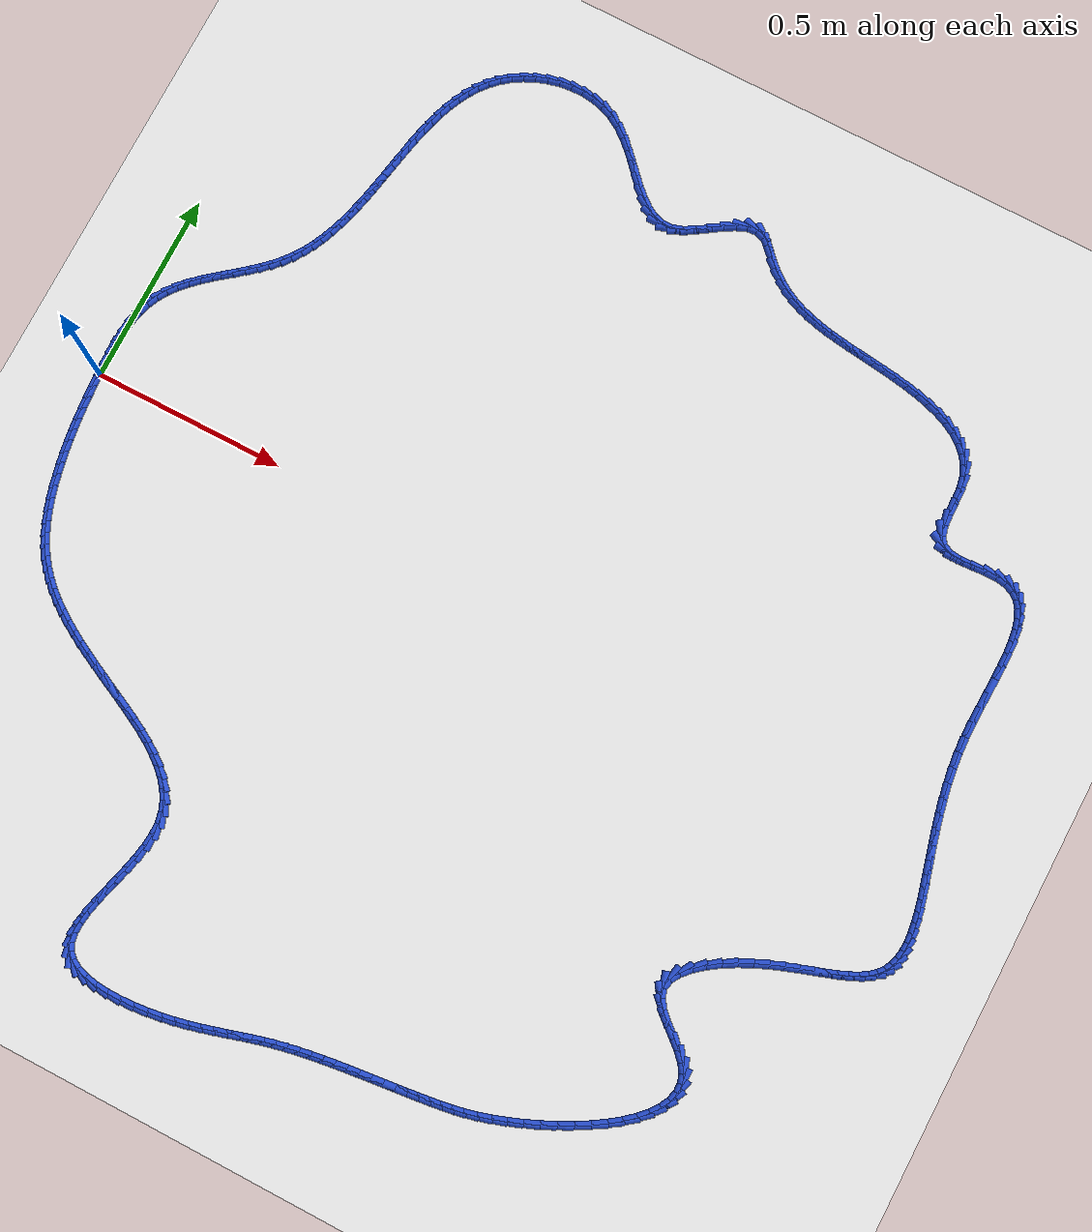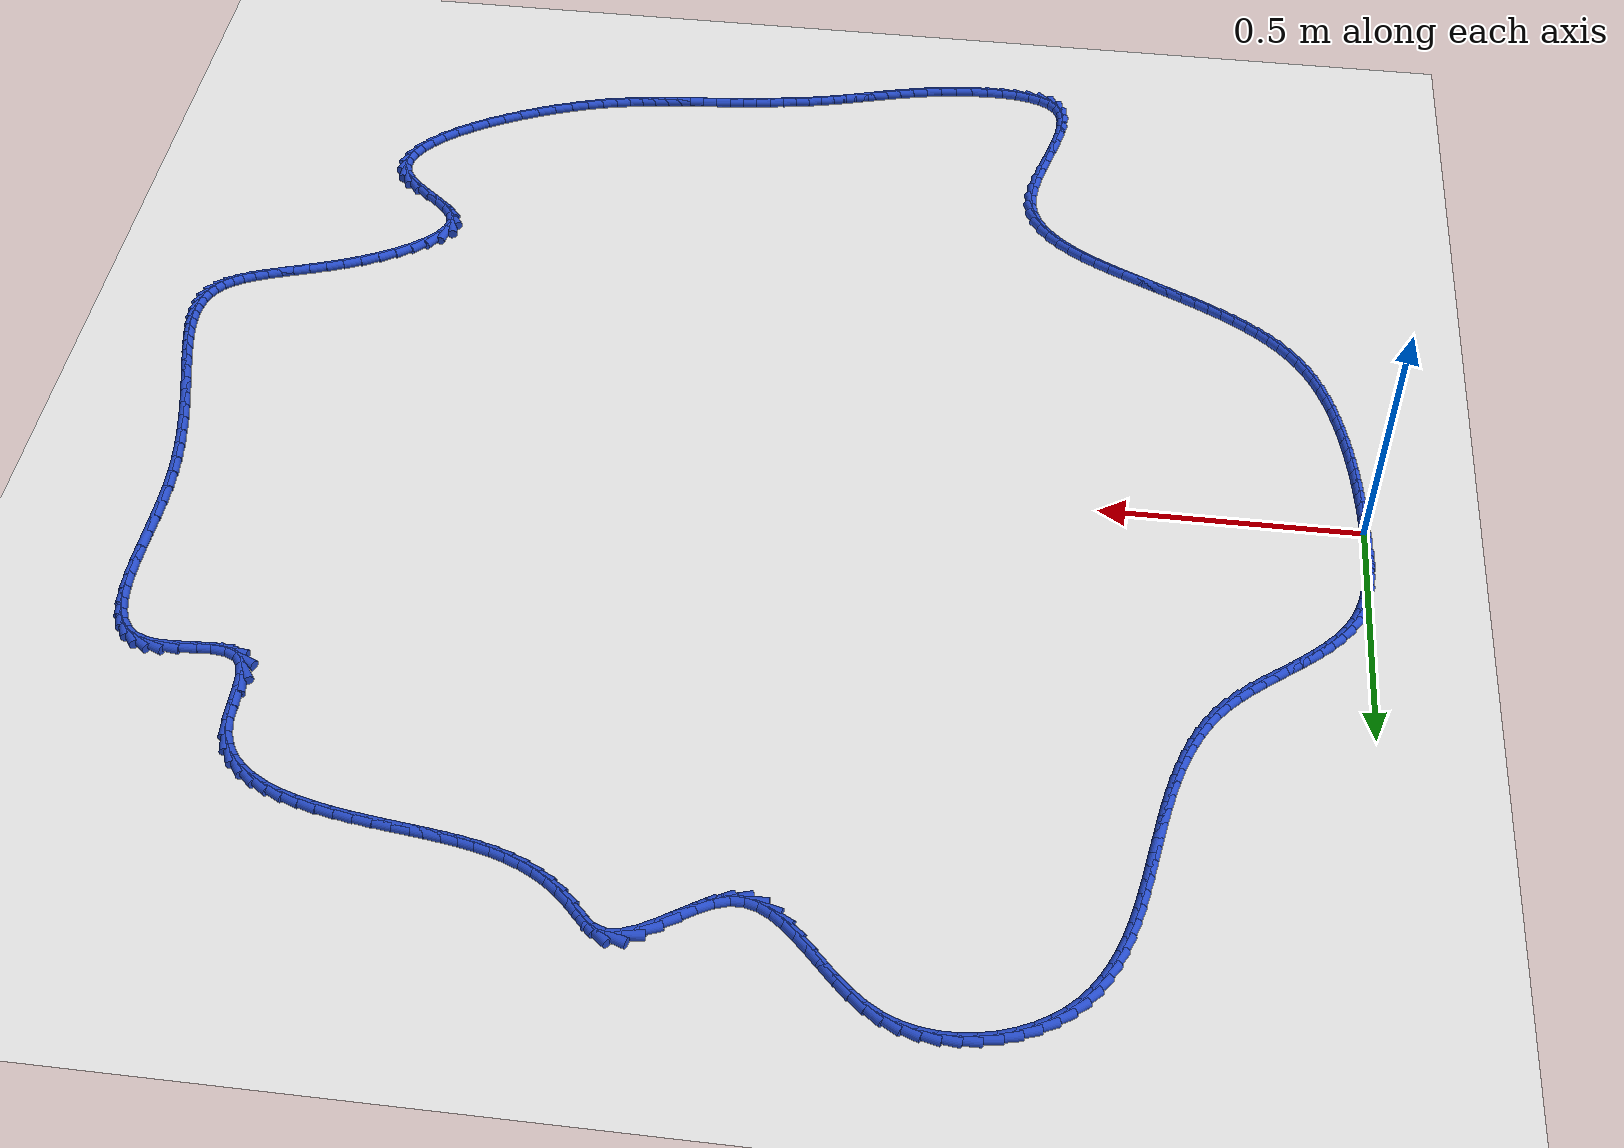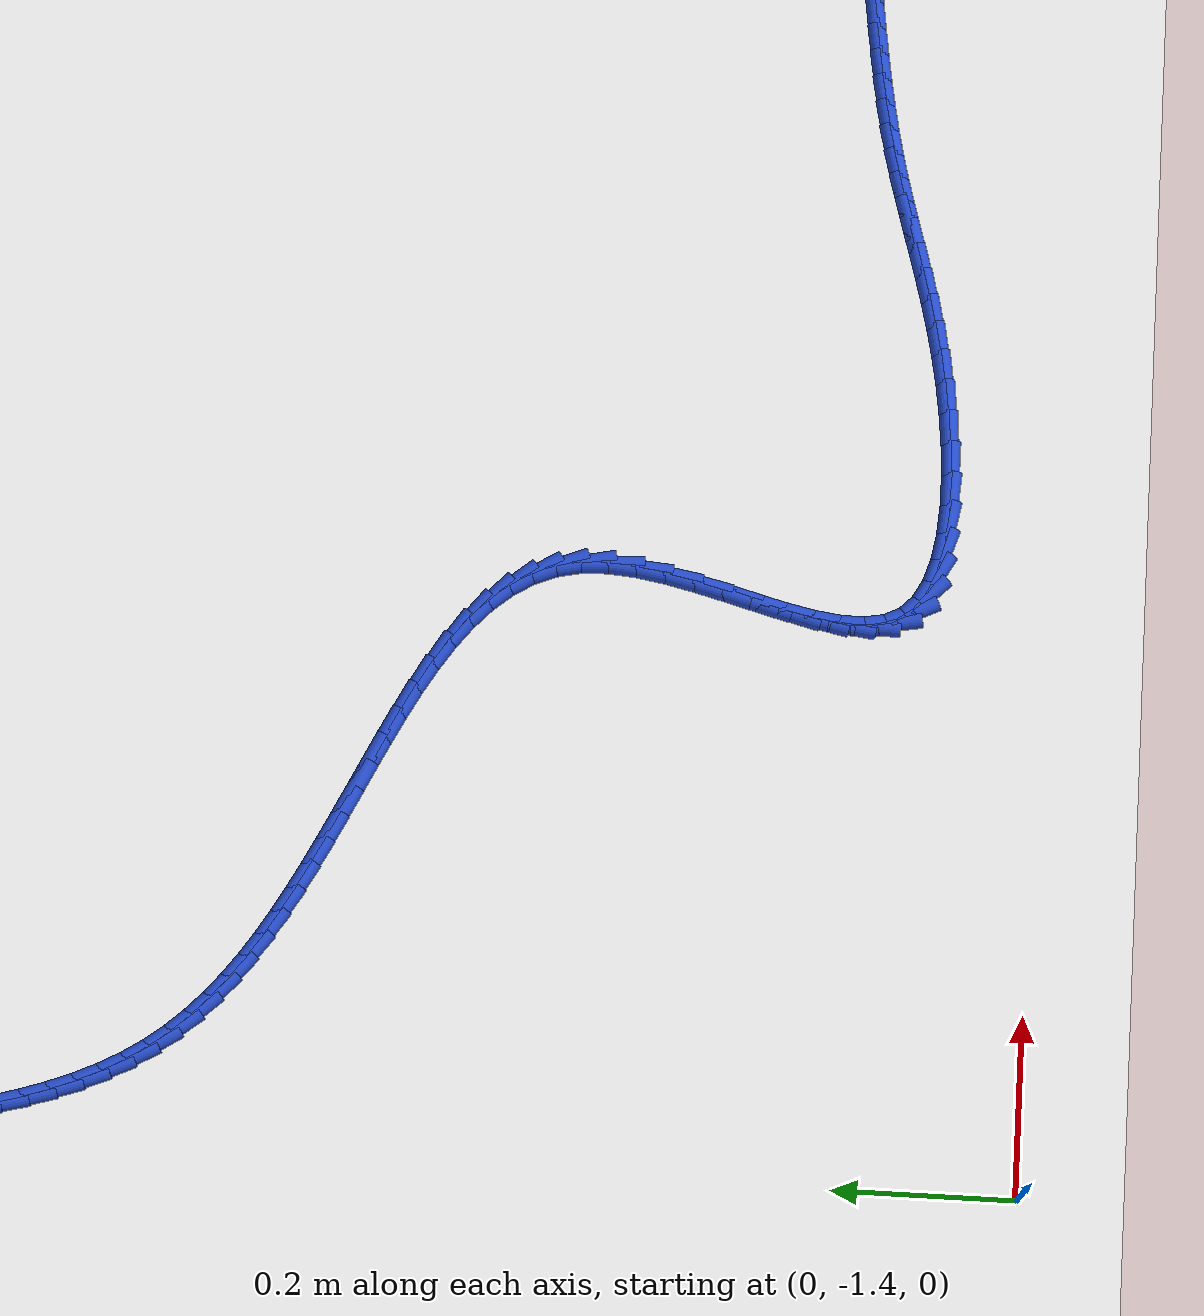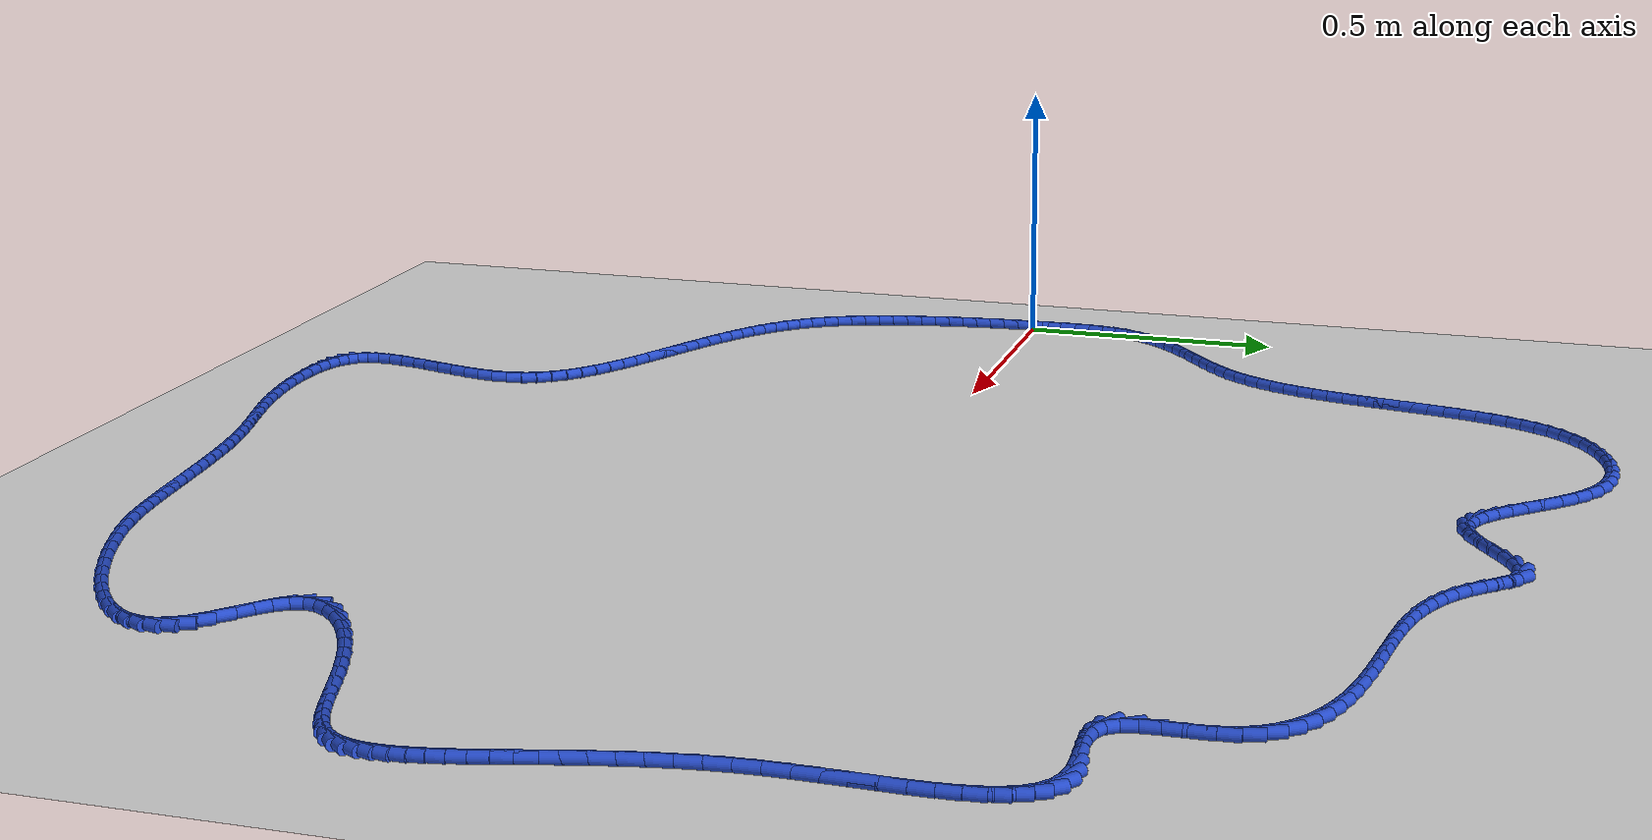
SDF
<sdf version="1.6">
 <world name="default">
  <light name="sun" type="directional">
   <pose>0 0 10 0 -0 0</pose>
   <diffuse>0.8 0.8 0.8 1</diffuse>
   <specular>0.2 0.2 0.2 1</specular>
   <attenuation>
    <range>1000</range>
    <constant>0.9</constant>
    <linear>0.01</linear>
    <quadratic>0.001</quadratic>
   </attenuation>
   <direction>-0.5 0.1 -0.9</direction>
  </light>
  <model name="ground_plane">
   <static>1</static>
   <link name="link">
    <collision name="collision">
     <geometry><plane><normal>0 0 1</normal><size>100 100</size></plane></geometry>
     <surface><friction><ode><mu>100</mu><mu2>50</mu2></ode></friction></surface>
    </collision>
    <visual name="visual">
     <cast_shadows>0</cast_shadows>
     <geometry><plane><normal>0 0 1</normal><size>100 100</size></plane></geometry>
     <material>
      <script><uri>file://media/materials/scripts/gazebo.material</uri><name>Gazebo/WhiteGlow</name></script>
     </material>
    </visual>
   </link>
  </model>
  <gravity>0 0 -9.8</gravity>
  <magnetic_field>6e-06 2.3e-05 -4.2e-05</magnetic_field>
  <atmosphere type="adiabatic"/>
  <physics name="default_physics" default="0" type="ode">
   <max_step_size>0.001</max_step_size>
   <real_time_factor>1</real_time_factor>
   <real_time_update_rate>1000</real_time_update_rate>
  </physics>
  <scene><ambient>0.4 0.4 0.4 1</ambient><background>0.7 0.7 0.7 1</background><shadows>1</shadows></scene>
  <spherical_coordinates>
   <surface_model>EARTH_WGS84</surface_model>
   <latitude_deg>0</latitude_deg>
   <longitude_deg>0</longitude_deg>
   <elevation>0</elevation>
   <heading_deg>0</heading_deg>
  </spherical_coordinates>
  <model name="line">
   <link name="link_0">
    <pose>8.456776945386935e-18 -2.7755575615628914e-17 0.01 0 1.57 -1.5227607795798939</pose>
    <collision name="collision">
     <geometry><cylinder><radius>0.01</radius><length>0.08</length></cylinder></geometry>
    </collision>
    <visual name="visual">
     <material>
      <script><name>Gazebo/Blue</name><uri>file://media/materials/scripts/gazebo.material</uri></script>
     </material>
     <geometry><cylinder><radius>0.01</radius><length>0.08</length></cylinder></geometry>
    </visual>
   </link>
   <link name="link_1">
    <pose>-0.0014766795499560638 0.030717743223473117 0.01 0 1.57 -1.5451004872439487</pose>
    <collision name="collision">
     <geometry><cylinder><radius>0.01</radius><length>0.08</length></cylinder></geometry>
    </collision>
    <visual name="visual">
     <material>
      <script><name>Gazebo/Blue</name><uri>file://media/materials/scripts/gazebo.material</uri></script>
     </material>
     <geometry><cylinder><radius>0.01</radius><length>0.08</length></cylinder></geometry>
    </visual>
   </link>
   <link name="link_2">
    <pose>-0.0022717804618448533 0.06165372051326525 0.01 0 1.57 1.5617429754365542</pose>
    <collision name="collision">
     <geometry><cylinder><radius>0.01</radius><length>0.08</length></cylinder></geometry>
    </collision>
    <visual name="visual">
     <material>
      <script><name>Gazebo/Blue</name><uri>file://media/materials/scripts/gazebo.material</uri></script>
     </material>
     <geometry><cylinder><radius>0.01</radius><length>0.08</length></cylinder></geometry>
    </visual>
   </link>
   <link name="link_3">
    <pose>-0.001992421770971372 0.09250981428451353 0.01 0 1.57 1.5135489547175613</pose>
    <collision name="collision">
     <geometry><cylinder><radius>0.01</radius><length>0.08</length></cylinder></geometry>
    </collision>
    <visual name="visual">
     <material>
      <script><name>Gazebo/Blue</name><uri>file://media/materials/scripts/gazebo.material</uri></script>
     </material>
     <geometry><cylinder><radius>0.01</radius><length>0.08</length></cylinder></geometry>
    </visual>
   </link>
   <link name="link_4">
    <pose>-0.0002457225126406325 0.12298790695235498 0.01 0 1.57 1.4503525471026657</pose>
    <collision name="collision">
     <geometry><cylinder><radius>0.01</radius><length>0.08</length></cylinder></geometry>
    </collision>
    <visual name="visual">
     <material>
      <script><name>Gazebo/Blue</name><uri>file://media/materials/scripts/gazebo.material</uri></script>
     </material>
     <geometry><cylinder><radius>0.01</radius><length>0.08</length></cylinder></geometry>
    </visual>
   </link>
   <link name="link_5">
    <pose>0.003361198277842349 0.15278988093192675 0.01 0 1.57 1.3702515587760018</pose>
    <collision name="collision">
     <geometry><cylinder><radius>0.01</radius><length>0.08</length></cylinder></geometry>
    </collision>
    <visual name="visual">
     <material>
      <script><name>Gazebo/Blue</name><uri>file://media/materials/scripts/gazebo.material</uri></script>
     </material>
     <geometry><cylinder><radius>0.01</radius><length>0.08</length></cylinder></geometry>
    </visual>
   </link>
   <link name="link_6">
    <pose>0.009221221565172568 0.18161761863836592 0.01 0 1.57 1.2713883890087878</pose>
    <collision name="collision">
     <geometry><cylinder><radius>0.01</radius><length>0.08</length></cylinder></geometry>
    </collision>
    <visual name="visual">
     <material>
      <script><name>Gazebo/Blue</name><uri>file://media/materials/scripts/gazebo.material</uri></script>
     </material>
     <geometry><cylinder><radius>0.01</radius><length>0.08</length></cylinder></geometry>
    </visual>
   </link>
   <link name="link_7">
    <pose>0.01772722831404501 0.20917300248680967 0.01 0 1.57 1.1527355143739297</pose>
    <collision name="collision">
     <geometry><cylinder><radius>0.01</radius><length>0.08</length></cylinder></geometry>
    </collision>
    <visual name="visual">
     <material>
      <script><name>Gazebo/Blue</name><uri>file://media/materials/scripts/gazebo.material</uri></script>
     </material>
     <geometry><cylinder><radius>0.01</radius><length>0.08</length></cylinder></geometry>
    </visual>
   </link>
   <link name="link_8">
    <pose>0.029271236593928593 0.23515846916683084 0.01 0 1.57 1.02523981779138</pose>
    <collision name="collision">
     <geometry><cylinder><radius>0.01</radius><length>0.08</length></cylinder></geometry>
    </collision>
    <visual name="visual">
     <material>
      <script><name>Gazebo/Blue</name><uri>file://media/materials/scripts/gazebo.material</uri></script>
     </material>
     <geometry><cylinder><radius>0.01</radius><length>0.08</length></cylinder></geometry>
    </visual>
   </link>
   <link name="link_9">
    <pose>0.044004804190127124 0.25943091327241796 0.01 0 1.57 0.915575742328255</pose>
    <collision name="collision">
     <geometry><cylinder><radius>0.01</radius><length>0.08</length></cylinder></geometry>
    </collision>
    <visual name="visual">
     <material>
      <script><name>Gazebo/Blue</name><uri>file://media/materials/scripts/gazebo.material</uri></script>
     </material>
     <geometry><cylinder><radius>0.01</radius><length>0.08</length></cylinder></geometry>
    </visual>
   </link>
   <link name="link_10">
    <pose>0.0615115360696729 0.28221204973544534 0.01 0 1.57 0.8284876100115119</pose>
    <collision name="collision">
     <geometry><cylinder><radius>0.01</radius><length>0.08</length></cylinder></geometry>
    </collision>
    <visual name="visual">
     <material>
      <script><name>Gazebo/Blue</name><uri>file://media/materials/scripts/gazebo.material</uri></script>
     </material>
     <geometry><cylinder><radius>0.01</radius><length>0.08</length></cylinder></geometry>
    </visual>
   </link>
   <link name="link_11">
    <pose>0.0812930656886783 0.3037762472881533 0.01 0 1.57 0.7632030751500273</pose>
    <collision name="collision">
     <geometry><cylinder><radius>0.01</radius><length>0.08</length></cylinder></geometry>
    </collision>
    <visual name="visual">
     <material>
      <script><name>Gazebo/Blue</name><uri>file://media/materials/scripts/gazebo.material</uri></script>
     </material>
     <geometry><cylinder><radius>0.01</radius><length>0.08</length></cylinder></geometry>
    </visual>
   </link>
   <link name="link_12">
    <pose>0.10285102650325569 0.32439787466278236 0.01 0 1.57 0.718132737947095</pose>
    <collision name="collision">
     <geometry><cylinder><radius>0.01</radius><length>0.08</length></cylinder></geometry>
    </collision>
    <visual name="visual">
     <material>
      <script><name>Gazebo/Blue</name><uri>file://media/materials/scripts/gazebo.material</uri></script>
     </material>
     <geometry><cylinder><radius>0.01</radius><length>0.08</length></cylinder></geometry>
    </visual>
   </link>
   <link name="link_13">
    <pose>0.12568705196951738 0.34435130059157315 0.01 0 1.57 0.6917275055884001</pose>
    <collision name="collision">
     <geometry><cylinder><radius>0.01</radius><length>0.08</length></cylinder></geometry>
    </collision>
    <visual name="visual">
     <material>
      <script><name>Gazebo/Blue</name><uri>file://media/materials/scripts/gazebo.material</uri></script>
     </material>
     <geometry><cylinder><radius>0.01</radius><length>0.08</length></cylinder></geometry>
    </visual>
   </link>
   <link name="link_14">
    <pose>0.14930277554357585 0.36391089380676617 0.01 0 1.57 0.6829154623494383</pose>
    <collision name="collision">
     <geometry><cylinder><radius>0.01</radius><length>0.08</length></cylinder></geometry>
    </collision>
    <visual name="visual">
     <material>
      <script><name>Gazebo/Blue</name><uri>file://media/materials/scripts/gazebo.material</uri></script>
     </material>
     <geometry><cylinder><radius>0.01</radius><length>0.08</length></cylinder></geometry>
    </visual>
   </link>
   <link name="link_15">
    <pose>0.17319983068154324 0.38335102304060165 0.01 0 1.57 0.6912811827394161</pose>
    <collision name="collision">
     <geometry><cylinder><radius>0.01</radius><length>0.08</length></cylinder></geometry>
    </collision>
    <visual name="visual">
     <material>
      <script><name>Gazebo/Blue</name><uri>file://media/materials/scripts/gazebo.material</uri></script>
     </material>
     <geometry><cylinder><radius>0.01</radius><length>0.08</length></cylinder></geometry>
    </visual>
   </link>
   <link name="link_16">
    <pose>0.1968798508395321 0.4029460570253205 0.01 0 1.57 0.7171075780058435</pose>
    <collision name="collision">
     <geometry><cylinder><radius>0.01</radius><length>0.08</length></cylinder></geometry>
    </collision>
    <visual name="visual">
     <material>
      <script><name>Gazebo/Blue</name><uri>file://media/materials/scripts/gazebo.material</uri></script>
     </material>
     <geometry><cylinder><radius>0.01</radius><length>0.08</length></cylinder></geometry>
    </visual>
   </link>
   <link name="link_17">
    <pose>0.21984446947365482 0.42297036449316294 0.01 0 1.57 0.7613225484306678</pose>
    <collision name="collision">
     <geometry><cylinder><radius>0.01</radius><length>0.08</length></cylinder></geometry>
    </collision>
    <visual name="visual">
     <material>
      <script><name>Gazebo/Blue</name><uri>file://media/materials/scripts/gazebo.material</uri></script>
     </material>
     <geometry><cylinder><radius>0.01</radius><length>0.08</length></cylinder></geometry>
    </visual>
   </link>
   <link name="link_18">
    <pose>0.24159532004002357 0.4436983141763696 0.01 0 1.57 0.8253160443918094</pose>
    <collision name="collision">
     <geometry><cylinder><radius>0.01</radius><length>0.08</length></cylinder></geometry>
    </collision>
    <visual name="visual">
     <material>
      <script><name>Gazebo/Blue</name><uri>file://media/materials/scripts/gazebo.material</uri></script>
     </material>
     <geometry><cylinder><radius>0.01</radius><length>0.08</length></cylinder></geometry>
    </visual>
   </link>
   <link name="link_19">
    <pose>0.2616340359947508 0.46540427480718094 0.01 0 1.57 0.9069009901010257</pose>
    <collision name="collision">
     <geometry><cylinder><radius>0.01</radius><length>0.08</length></cylinder></geometry>
    </collision>
    <visual name="visual">
     <material>
      <script><name>Gazebo/Blue</name><uri>file://media/materials/scripts/gazebo.material</uri></script>
     </material>
     <geometry><cylinder><radius>0.01</radius><length>0.08</length></cylinder></geometry>
    </visual>
   </link>
   <link name="link_20">
    <pose>0.2795564527115686 0.4883122586597587 0.01 0 1.57 0.9886346267813351</pose>
    <collision name="collision">
     <geometry><cylinder><radius>0.01</radius><length>0.08</length></cylinder></geometry>
    </collision>
    <visual name="visual">
     <material>
      <script><name>Gazebo/Blue</name><uri>file://media/materials/scripts/gazebo.material</uri></script>
     </material>
     <geometry><cylinder><radius>0.01</radius><length>0.08</length></cylinder></geometry>
    </visual>
   </link>
   <link name="link_21">
    <pose>0.2954142285881841 0.5124026138284027 0.01 0 1.57 1.063883537466776</pose>
    <collision name="collision">
     <geometry><cylinder><radius>0.01</radius><length>0.08</length></cylinder></geometry>
    </collision>
    <visual name="visual">
     <material>
      <script><name>Gazebo/Blue</name><uri>file://media/materials/scripts/gazebo.material</uri></script>
     </material>
     <geometry><cylinder><radius>0.01</radius><length>0.08</length></cylinder></geometry>
    </visual>
   </link>
   <link name="link_22">
    <pose>0.3093967064856879 0.5375820879746012 0.01 0 1.57 1.1316185422971006</pose>
    <collision name="collision">
     <geometry><cylinder><radius>0.01</radius><length>0.08</length></cylinder></geometry>
    </collision>
    <visual name="visual">
     <material>
      <script><name>Gazebo/Blue</name><uri>file://media/materials/scripts/gazebo.material</uri></script>
     </material>
     <geometry><cylinder><radius>0.01</radius><length>0.08</length></cylinder></geometry>
    </visual>
   </link>
   <link name="link_23">
    <pose>0.3216932583514957 0.5637574132114931 0.01 0 1.57 1.1912825503669429</pose>
    <collision name="collision">
     <geometry><cylinder><radius>0.01</radius><length>0.08</length></cylinder></geometry>
    </collision>
    <visual name="visual">
     <material>
      <script><name>Gazebo/Blue</name><uri>file://media/materials/scripts/gazebo.material</uri></script>
     </material>
     <geometry><cylinder><radius>0.01</radius><length>0.08</length></cylinder></geometry>
    </visual>
   </link>
   <link name="link_24">
    <pose>0.3324932561330238 0.590835321652218 0.01 0 1.57 1.2426991619687908</pose>
    <collision name="collision">
     <geometry><cylinder><radius>0.01</radius><length>0.08</length></cylinder></geometry>
    </collision>
    <visual name="visual">
     <material>
      <script><name>Gazebo/Blue</name><uri>file://media/materials/scripts/gazebo.material</uri></script>
     </material>
     <geometry><cylinder><radius>0.01</radius><length>0.08</length></cylinder></geometry>
    </visual>
   </link>
   <link name="link_25">
    <pose>0.3419860717776878 0.6187225454099143 0.01 0 1.57 1.2859590976979571</pose>
    <collision name="collision">
     <geometry><cylinder><radius>0.01</radius><length>0.08</length></cylinder></geometry>
    </collision>
    <visual name="visual">
     <material>
      <script><name>Gazebo/Blue</name><uri>file://media/materials/scripts/gazebo.material</uri></script>
     </material>
     <geometry><cylinder><radius>0.01</radius><length>0.08</length></cylinder></geometry>
    </visual>
   </link>
   <link name="link_26">
    <pose>0.3503610772329039 0.6473258165977218 0.01 0 1.57 1.3213125501815395</pose>
    <collision name="collision">
     <geometry><cylinder><radius>0.01</radius><length>0.08</length></cylinder></geometry>
    </collision>
    <visual name="visual">
     <material>
      <script><name>Gazebo/Blue</name><uri>file://media/materials/scripts/gazebo.material</uri></script>
     </material>
     <geometry><cylinder><radius>0.01</radius><length>0.08</length></cylinder></geometry>
    </visual>
   </link>
   <link name="link_27">
    <pose>0.35780764444608765 0.6765518673287787 0.01 0 1.57 1.3490820929666452</pose>
    <collision name="collision">
     <geometry><cylinder><radius>0.01</radius><length>0.08</length></cylinder></geometry>
    </collision>
    <visual name="visual">
     <material>
      <script><name>Gazebo/Blue</name><uri>file://media/materials/scripts/gazebo.material</uri></script>
     </material>
     <geometry><cylinder><radius>0.01</radius><length>0.08</length></cylinder></geometry>
    </visual>
   </link>
   <link name="link_28">
    <pose>0.3645151453646553 0.7063074297162247 0.01 0 1.57 1.369599622309432</pose>
    <collision name="collision">
     <geometry><cylinder><radius>0.01</radius><length>0.08</length></cylinder></geometry>
    </collision>
    <visual name="visual">
     <material>
      <script><name>Gazebo/Blue</name><uri>file://media/materials/scripts/gazebo.material</uri></script>
     </material>
     <geometry><cylinder><radius>0.01</radius><length>0.08</length></cylinder></geometry>
    </visual>
   </link>
   <link name="link_29">
    <pose>0.37067295193602257 0.7364992358731985 0.01 0 1.57 1.383164749995835</pose>
    <collision name="collision">
     <geometry><cylinder><radius>0.01</radius><length>0.08</length></cylinder></geometry>
    </collision>
    <visual name="visual">
     <material>
      <script><name>Gazebo/Blue</name><uri>file://media/materials/scripts/gazebo.material</uri></script>
     </material>
     <geometry><cylinder><radius>0.01</radius><length>0.08</length></cylinder></geometry>
    </visual>
   </link>
   <link name="link_30">
    <pose>0.37647043610760544 0.7670340179128394 0.01 0 1.57 1.390019972079069</pose>
    <collision name="collision">
     <geometry><cylinder><radius>0.01</radius><length>0.08</length></cylinder></geometry>
    </collision>
    <visual name="visual">
     <material>
      <script><name>Gazebo/Blue</name><uri>file://media/materials/scripts/gazebo.material</uri></script>
     </material>
     <geometry><cylinder><radius>0.01</radius><length>0.08</length></cylinder></geometry>
    </visual>
   </link>
   <link name="link_31">
    <pose>0.38209696982681984 0.7978185079482861 0.01 0 1.57 1.3903380978581459</pose>
    <collision name="collision">
     <geometry><cylinder><radius>0.01</radius><length>0.08</length></cylinder></geometry>
    </collision>
    <visual name="visual">
     <material>
      <script><name>Gazebo/Blue</name><uri>file://media/materials/scripts/gazebo.material</uri></script>
     </material>
     <geometry><cylinder><radius>0.01</radius><length>0.08</length></cylinder></geometry>
    </visual>
   </link>
   <link name="link_32">
    <pose>0.3877419250410815 0.8287594380926777 0.01 0 1.57 1.3842147053571736</pose>
    <collision name="collision">
     <geometry><cylinder><radius>0.01</radius><length>0.08</length></cylinder></geometry>
    </collision>
    <visual name="visual">
     <material>
      <script><name>Gazebo/Blue</name><uri>file://media/materials/scripts/gazebo.material</uri></script>
     </material>
     <geometry><cylinder><radius>0.01</radius><length>0.08</length></cylinder></geometry>
    </visual>
   </link>
   <link name="link_33">
    <pose>0.3935947596824988 0.8597633428944247 0.01 0 1.57 1.3709828750161386</pose>
    <collision name="collision">
     <geometry><cylinder><radius>0.01</radius><length>0.08</length></cylinder></geometry>
    </collision>
    <visual name="visual">
     <material>
      <script><name>Gazebo/Blue</name><uri>file://media/materials/scripts/gazebo.material</uri></script>
     </material>
     <geometry><cylinder><radius>0.01</radius><length>0.08</length></cylinder></geometry>
    </visual>
   </link>
   <link name="link_34">
    <pose>0.3998602421210087 0.8907015785181126 0.01 0 1.57 1.3490066683193687</pose>
    <collision name="collision">
     <geometry><cylinder><radius>0.01</radius><length>0.08</length></cylinder></geometry>
    </collision>
    <visual name="visual">
     <material>
      <script><name>Gazebo/Blue</name><uri>file://media/materials/scripts/gazebo.material</uri></script>
     </material>
     <geometry><cylinder><radius>0.01</radius><length>0.08</length></cylinder></geometry>
    </visual>
   </link>
   <link name="link_35">
    <pose>0.40677596760440515 0.9213700756883832 0.01 0 1.57 1.3176785860591123</pose>
    <collision name="collision">
     <geometry><cylinder><radius>0.01</radius><length>0.08</length></cylinder></geometry>
    </collision>
    <visual name="visual">
     <material>
      <script><name>Gazebo/Blue</name><uri>file://media/materials/scripts/gazebo.material</uri></script>
     </material>
     <geometry><cylinder><radius>0.01</radius><length>0.08</length></cylinder></geometry>
    </visual>
   </link>
   <link name="link_36">
    <pose>0.4145837736025517 0.9515550178896063 0.01 0 1.57 1.276372413049469</pose>
    <collision name="collision">
     <geometry><cylinder><radius>0.01</radius><length>0.08</length></cylinder></geometry>
    </collision>
    <visual name="visual">
     <material>
      <script><name>Gazebo/Blue</name><uri>file://media/materials/scripts/gazebo.material</uri></script>
     </material>
     <geometry><cylinder><radius>0.01</radius><length>0.08</length></cylinder></geometry>
    </visual>
   </link>
   <link name="link_37">
    <pose>0.42352549758531144 0.9810425886061497 0.01 0 1.57 1.2243122536844446</pose>
    <collision name="collision">
     <geometry><cylinder><radius>0.01</radius><length>0.08</length></cylinder></geometry>
    </collision>
    <visual name="visual">
     <material>
      <script><name>Gazebo/Blue</name><uri>file://media/materials/scripts/gazebo.material</uri></script>
     </material>
     <geometry><cylinder><radius>0.01</radius><length>0.08</length></cylinder></geometry>
    </visual>
   </link>
   <link name="link_38">
    <pose>0.43384297702254754 1.0096189713223822 0.01 0 1.57 1.1606784672435109</pose>
    <collision name="collision">
     <geometry><cylinder><radius>0.01</radius><length>0.08</length></cylinder></geometry>
    </collision>
    <visual name="visual">
     <material>
      <script><name>Gazebo/Blue</name><uri>file://media/materials/scripts/gazebo.material</uri></script>
     </material>
     <geometry><cylinder><radius>0.01</radius><length>0.08</length></cylinder></geometry>
    </visual>
   </link>
   <link name="link_39">
    <pose>0.445778049384123 1.0370703495226725 0.01 0 1.57 1.0847886627277465</pose>
    <collision name="collision">
     <geometry><cylinder><radius>0.01</radius><length>0.08</length></cylinder></geometry>
    </collision>
    <visual name="visual">
     <material>
      <script><name>Gazebo/Blue</name><uri>file://media/materials/scripts/gazebo.material</uri></script>
     </material>
     <geometry><cylinder><radius>0.01</radius><length>0.08</length></cylinder></geometry>
    </visual>
   </link>
   <link name="link_40">
    <pose>0.45957255213990134 1.0631829066913896 0.01 0 1.57 0.9963750416095719</pose>
    <collision name="collision">
     <geometry><cylinder><radius>0.01</radius><length>0.08</length></cylinder></geometry>
    </collision>
    <visual name="visual">
     <material>
      <script><name>Gazebo/Blue</name><uri>file://media/materials/scripts/gazebo.material</uri></script>
     </material>
     <geometry><cylinder><radius>0.01</radius><length>0.08</length></cylinder></geometry>
    </visual>
   </link>
   <link name="link_41">
    <pose>0.4754683227597457 1.0877428263129019 0.01 0 1.57 0.8959456198416729</pose>
    <collision name="collision">
     <geometry><cylinder><radius>0.01</radius><length>0.08</length></cylinder></geometry>
    </collision>
    <visual name="visual">
     <material>
      <script><name>Gazebo/Blue</name><uri>file://media/materials/scripts/gazebo.material</uri></script>
     </material>
     <geometry><cylinder><radius>0.01</radius><length>0.08</length></cylinder></geometry>
    </visual>
   </link>
   <link name="link_42">
    <pose>0.49370719871351926 1.110536291871578 0.01 0 1.57 0.7851430111621526</pose>
    <collision name="collision">
     <geometry><cylinder><radius>0.01</radius><length>0.08</length></cylinder></geometry>
    </collision>
    <visual name="visual">
     <material>
      <script><name>Gazebo/Blue</name><uri>file://media/materials/scripts/gazebo.material</uri></script>
     </material>
     <geometry><cylinder><radius>0.01</radius><length>0.08</length></cylinder></geometry>
    </visual>
   </link>
   <link name="link_43">
    <pose>0.5145310174710853 1.1313494868517873 0.01 0 1.57 0.6679692432426003</pose>
    <collision name="collision">
     <geometry><cylinder><radius>0.01</radius><length>0.08</length></cylinder></geometry>
    </collision>
    <visual name="visual">
     <material>
      <script><name>Gazebo/Blue</name><uri>file://media/materials/scripts/gazebo.material</uri></script>
     </material>
     <geometry><cylinder><radius>0.01</radius><length>0.08</length></cylinder></geometry>
    </visual>
   </link>
   <link name="link_44">
    <pose>0.5381275358078345 1.1499660563740692 0.01 0 1.57 0.5547264463963215</pose>
    <collision name="collision">
     <geometry><cylinder><radius>0.01</radius><length>0.08</length></cylinder></geometry>
    </collision>
    <visual name="visual">
     <material>
      <script><name>Gazebo/Blue</name><uri>file://media/materials/scripts/gazebo.material</uri></script>
     </material>
     <geometry><cylinder><radius>0.01</radius><length>0.08</length></cylinder></geometry>
    </visual>
   </link>
   <link name="link_45">
    <pose>0.5642447678131123 1.1661490055331876 0.01 0 1.57 0.44693477517919256</pose>
    <collision name="collision">
     <geometry><cylinder><radius>0.01</radius><length>0.08</length></cylinder></geometry>
    </collision>
    <visual name="visual">
     <material>
      <script><name>Gazebo/Blue</name><uri>file://media/materials/scripts/gazebo.material</uri></script>
     </material>
     <geometry><cylinder><radius>0.01</radius><length>0.08</length></cylinder></geometry>
    </visual>
   </link>
   <link name="link_46">
    <pose>0.5924167917291747 1.1796512980030045 0.01 0 1.57 0.34141825438717727</pose>
    <collision name="collision">
     <geometry><cylinder><radius>0.01</radius><length>0.08</length></cylinder></geometry>
    </collision>
    <visual name="visual">
     <material>
      <script><name>Gazebo/Blue</name><uri>file://media/materials/scripts/gazebo.material</uri></script>
     </material>
     <geometry><cylinder><radius>0.01</radius><length>0.08</length></cylinder></geometry>
    </visual>
   </link>
   <link name="link_47">
    <pose>0.6221762583141995 1.190225830456135 0.01 0 1.57 0.23519510703398594</pose>
    <collision name="collision">
     <geometry><cylinder><radius>0.01</radius><length>0.08</length></cylinder></geometry>
    </collision>
    <visual name="visual">
     <material>
      <script><name>Gazebo/Blue</name><uri>file://media/materials/scripts/gazebo.material</uri></script>
     </material>
     <geometry><cylinder><radius>0.01</radius><length>0.08</length></cylinder></geometry>
    </visual>
   </link>
   <link name="link_48">
    <pose>0.6530558183263643 1.1976254995651947 0.01 0 1.57 0.12548409048501724</pose>
    <collision name="collision">
     <geometry><cylinder><radius>0.01</radius><length>0.08</length></cylinder></geometry>
    </collision>
    <visual name="visual">
     <material>
      <script><name>Gazebo/Blue</name><uri>file://media/materials/scripts/gazebo.material</uri></script>
     </material>
     <geometry><cylinder><radius>0.01</radius><length>0.08</length></cylinder></geometry>
    </visual>
   </link>
   <link name="link_49">
    <pose>0.6845881225238463 1.2016032020027996 0.01 0 1.57 0.009730299068164599</pose>
    <collision name="collision">
     <geometry><cylinder><radius>0.01</radius><length>0.08</length></cylinder></geometry>
    </collision>
    <visual name="visual">
     <material>
      <script><name>Gazebo/Blue</name><uri>file://media/materials/scripts/gazebo.material</uri></script>
     </material>
     <geometry><cylinder><radius>0.01</radius><length>0.08</length></cylinder></geometry>
    </visual>
   </link>
   <link name="link_50">
    <pose>0.7163058216648232 1.201911834441565 0.01 0 1.57 -0.11425936196864711</pose>
    <collision name="collision">
     <geometry><cylinder><radius>0.01</radius><length>0.08</length></cylinder></geometry>
    </collision>
    <visual name="visual">
     <material>
      <script><name>Gazebo/Blue</name><uri>file://media/materials/scripts/gazebo.material</uri></script>
     </material>
     <geometry><cylinder><radius>0.01</radius><length>0.08</length></cylinder></geometry>
    </visual>
   </link>
   <link name="link_51">
    <pose>0.747741566507472 1.1983042935541062 0.01 0 1.57 -0.24801910159536206</pose>
    <collision name="collision">
     <geometry><cylinder><radius>0.01</radius><length>0.08</length></cylinder></geometry>
    </collision>
    <visual name="visual">
     <material>
      <script><name>Gazebo/Blue</name><uri>file://media/materials/scripts/gazebo.material</uri></script>
     </material>
     <geometry><cylinder><radius>0.01</radius><length>0.08</length></cylinder></geometry>
    </visual>
   </link>
   <link name="link_52">
    <pose>0.7784280078099711 1.1905334760130386 0.01 0 1.57 -0.39195771539659013</pose>
    <collision name="collision">
     <geometry><cylinder><radius>0.01</radius><length>0.08</length></cylinder></geometry>
    </collision>
    <visual name="visual">
     <material>
      <script><name>Gazebo/Blue</name><uri>file://media/materials/scripts/gazebo.material</uri></script>
     </material>
     <geometry><cylinder><radius>0.01</radius><length>0.08</length></cylinder></geometry>
    </visual>
   </link>
   <link name="link_53">
    <pose>0.8078977963304974 1.178352278490978 0.01 0 1.57 -0.5423520050847065</pose>
    <collision name="collision">
     <geometry><cylinder><radius>0.01</radius><length>0.08</length></cylinder></geometry>
    </collision>
    <visual name="visual">
     <material>
      <script><name>Gazebo/Blue</name><uri>file://media/materials/scripts/gazebo.material</uri></script>
     </material>
     <geometry><cylinder><radius>0.01</radius><length>0.08</length></cylinder></geometry>
    </visual>
   </link>
   <link name="link_54">
    <pose>0.8357206865037328 1.1615853351074148 0.01 0 1.57 -0.6681780196593755</pose>
    <collision name="collision">
     <geometry><cylinder><radius>0.01</radius><length>0.08</length></cylinder></geometry>
    </collision>
    <visual name="visual">
     <material>
      <script><name>Gazebo/Blue</name><uri>file://media/materials/scripts/gazebo.material</uri></script>
     </material>
     <geometry><cylinder><radius>0.01</radius><length>0.08</length></cylinder></geometry>
    </visual>
   </link>
   <link name="link_55">
    <pose>0.8619097831241248 1.1409144678908958 0.01 0 1.57 -0.753626723761245</pose>
    <collision name="collision">
     <geometry><cylinder><radius>0.01</radius><length>0.08</length></cylinder></geometry>
    </collision>
    <visual name="visual">
     <material>
      <script><name>Gazebo/Blue</name><uri>file://media/materials/scripts/gazebo.material</uri></script>
     </material>
     <geometry><cylinder><radius>0.01</radius><length>0.08</length></cylinder></geometry>
    </visual>
   </link>
   <link name="link_56">
    <pose>0.8867700365199137 1.117585762453762 0.01 0 1.57 -0.8036997205169869</pose>
    <collision name="collision">
     <geometry><cylinder><radius>0.01</radius><length>0.08</length></cylinder></geometry>
    </collision>
    <visual name="visual">
     <material>
      <script><name>Gazebo/Blue</name><uri>file://media/materials/scripts/gazebo.material</uri></script>
     </material>
     <geometry><cylinder><radius>0.01</radius><length>0.08</length></cylinder></geometry>
    </visual>
   </link>
   <link name="link_57">
    <pose>0.9106115290743507 1.092855226889318 0.01 0 1.57 -0.8216990933541376</pose>
    <collision name="collision">
     <geometry><cylinder><radius>0.01</radius><length>0.08</length></cylinder></geometry>
    </collision>
    <visual name="visual">
     <material>
      <script><name>Gazebo/Blue</name><uri>file://media/materials/scripts/gazebo.material</uri></script>
     </material>
     <geometry><cylinder><radius>0.01</radius><length>0.08</length></cylinder></geometry>
    </visual>
   </link>
   <link name="link_58">
    <pose>0.9337443431706884 1.0679788692908685 0.01 0 1.57 -0.8075868840673326</pose>
    <collision name="collision">
     <geometry><cylinder><radius>0.01</radius><length>0.08</length></cylinder></geometry>
    </collision>
    <visual name="visual">
     <material>
      <script><name>Gazebo/Blue</name><uri>file://media/materials/scripts/gazebo.material</uri></script>
     </material>
     <geometry><cylinder><radius>0.01</radius><length>0.08</length></cylinder></geometry>
    </visual>
   </link>
   <link name="link_59">
    <pose>0.9564785611921783 1.0442126977517183 0.01 0 1.57 -0.7571230885375823</pose>
    <collision name="collision">
     <geometry><cylinder><radius>0.01</radius><length>0.08</length></cylinder></geometry>
    </collision>
    <visual name="visual">
     <material>
      <script><name>Gazebo/Blue</name><uri>file://media/materials/scripts/gazebo.material</uri></script>
     </material>
     <geometry><cylinder><radius>0.01</radius><length>0.08</length></cylinder></geometry>
    </visual>
   </link>
   <link name="link_60">
    <pose>0.9791242655220727 1.0228127203651722 0.01 0 1.57 -0.6608283773014858</pose>
    <collision name="collision">
     <geometry><cylinder><radius>0.01</radius><length>0.08</length></cylinder></geometry>
    </collision>
    <visual name="visual">
     <material>
      <script><name>Gazebo/Blue</name><uri>file://media/materials/scripts/gazebo.material</uri></script>
     </material>
     <geometry><cylinder><radius>0.01</radius><length>0.08</length></cylinder></geometry>
    </visual>
   </link>
   <link name="link_61">
    <pose>1.0019915385436233 1.0050349452245353 0.01 0 1.57 -0.5038321546648872</pose>
    <collision name="collision">
     <geometry><cylinder><radius>0.01</radius><length>0.08</length></cylinder></geometry>
    </collision>
    <visual name="visual">
     <material>
      <script><name>Gazebo/Blue</name><uri>file://media/materials/scripts/gazebo.material</uri></script>
     </material>
     <geometry><cylinder><radius>0.01</radius><length>0.08</length></cylinder></geometry>
    </visual>
   </link>
   <link name="link_62">
    <pose>1.025390462640082 0.9921353804231121 0.01 0 1.57 -0.27216547448522604</pose>
    <collision name="collision">
     <geometry><cylinder><radius>0.01</radius><length>0.08</length></cylinder></geometry>
    </collision>
    <visual name="visual">
     <material>
      <script><name>Gazebo/Blue</name><uri>file://media/materials/scripts/gazebo.material</uri></script>
     </material>
     <geometry><cylinder><radius>0.01</radius><length>0.08</length></cylinder></geometry>
    </visual>
   </link>
   <link name="link_63">
    <pose>1.0496311201947006 0.985370034054207 0.01 0 1.57 0.024603907276591834</pose>
    <collision name="collision">
     <geometry><cylinder><radius>0.01</radius><length>0.08</length></cylinder></geometry>
    </collision>
    <visual name="visual">
     <material>
      <script><name>Gazebo/Blue</name><uri>file://media/materials/scripts/gazebo.material</uri></script>
     </material>
     <geometry><cylinder><radius>0.01</radius><length>0.08</length></cylinder></geometry>
    </visual>
   </link>
   <link name="link_64">
    <pose>1.0750235935907315 0.9859949142111255 0.01 0 1.57 0.3192370790498513</pose>
    <collision name="collision">
     <geometry><cylinder><radius>0.01</radius><length>0.08</length></cylinder></geometry>
    </collision>
    <visual name="visual">
     <material>
      <script><name>Gazebo/Blue</name><uri>file://media/materials/scripts/gazebo.material</uri></script>
     </material>
     <geometry><cylinder><radius>0.01</radius><length>0.08</length></cylinder></geometry>
    </visual>
   </link>
   <link name="link_65">
    <pose>1.101796402133849 0.9948444763884836 0.01 0 1.57 0.4994906150765822</pose>
    <collision name="collision">
     <geometry><cylinder><radius>0.01</radius><length>0.08</length></cylinder></geometry>
    </collision>
    <visual name="visual">
     <material>
      <script><name>Gazebo/Blue</name><uri>file://media/materials/scripts/gazebo.material</uri></script>
     </material>
     <geometry><cylinder><radius>0.01</radius><length>0.08</length></cylinder></geometry>
    </visual>
   </link>
   <link name="link_66">
    <pose>1.1296540316333232 1.0100447485819546 0.01 0 1.57 0.5793380476691669</pose>
    <collision name="collision">
     <geometry><cylinder><radius>0.01</radius><length>0.08</length></cylinder></geometry>
    </collision>
    <visual name="visual">
     <material>
      <script><name>Gazebo/Blue</name><uri>file://media/materials/scripts/gazebo.material</uri></script>
     </material>
     <geometry><cylinder><radius>0.01</radius><length>0.08</length></cylinder></geometry>
    </visual>
   </link>
   <link name="link_67">
    <pose>1.1580937258659083 1.0286506440137233 0.01 0 1.57 0.5892507064706672</pose>
    <collision name="collision">
     <geometry><cylinder><radius>0.01</radius><length>0.08</length></cylinder></geometry>
    </collision>
    <visual name="visual">
     <material>
      <script><name>Gazebo/Blue</name><uri>file://media/materials/scripts/gazebo.material</uri></script>
     </material>
     <geometry><cylinder><radius>0.01</radius><length>0.08</length></cylinder></geometry>
    </visual>
   </link>
   <link name="link_68">
    <pose>1.1866122161454762 1.0477144272803147 0.01 0 1.57 0.5329935872585462</pose>
    <collision name="collision">
     <geometry><cylinder><radius>0.01</radius><length>0.08</length></cylinder></geometry>
    </collision>
    <visual name="visual">
     <material>
      <script><name>Gazebo/Blue</name><uri>file://media/materials/scripts/gazebo.material</uri></script>
     </material>
     <geometry><cylinder><radius>0.01</radius><length>0.08</length></cylinder></geometry>
    </visual>
   </link>
   <link name="link_69">
    <pose>1.2147062337858978 1.0642883629782538 0.01 0 1.57 0.3890398582765149</pose>
    <collision name="collision">
     <geometry><cylinder><radius>0.01</radius><length>0.08</length></cylinder></geometry>
    </collision>
    <visual name="visual">
     <material>
      <script><name>Gazebo/Blue</name><uri>file://media/materials/scripts/gazebo.material</uri></script>
     </material>
     <geometry><cylinder><radius>0.01</radius><length>0.08</length></cylinder></geometry>
    </visual>
   </link>
   <link name="link_70">
    <pose>1.2418725101010437 1.0754247157040653 0.01 0 1.57 0.10649304468396537</pose>
    <collision name="collision">
     <geometry><cylinder><radius>0.01</radius><length>0.08</length></cylinder></geometry>
    </collision>
    <visual name="visual">
     <material>
      <script><name>Gazebo/Blue</name><uri>file://media/materials/scripts/gazebo.material</uri></script>
     </material>
     <geometry><cylinder><radius>0.01</radius><length>0.08</length></cylinder></geometry>
    </visual>
   </link>
   <link name="link_71">
    <pose>1.2676077764047866 1.0781757500542746 0.01 0 1.57 -0.34252006664495893</pose>
    <collision name="collision">
     <geometry><cylinder><radius>0.01</radius><length>0.08</length></cylinder></geometry>
    </collision>
    <visual name="visual">
     <material>
      <script><name>Gazebo/Blue</name><uri>file://media/materials/scripts/gazebo.material</uri></script>
     </material>
     <geometry><cylinder><radius>0.01</radius><length>0.08</length></cylinder></geometry>
    </visual>
   </link>
   <link name="link_72">
    <pose>1.2914257842902765 1.0696828482767677 0.01 0 1.57 -0.7044989865022698</pose>
    <collision name="collision">
     <geometry><cylinder><radius>0.01</radius><length>0.08</length></cylinder></geometry>
    </collision>
    <visual name="visual">
     <material>
      <script><name>Gazebo/Blue</name><uri>file://media/materials/scripts/gazebo.material</uri></script>
     </material>
     <geometry><cylinder><radius>0.01</radius><length>0.08</length></cylinder></geometry>
    </visual>
   </link>
   <link name="link_73">
    <pose>1.313562100103759 1.0508667921497115 0.01 0 1.57 -0.8178600807181006</pose>
    <collision name="collision">
     <geometry><cylinder><radius>0.01</radius><length>0.08</length></cylinder></geometry>
    </collision>
    <visual name="visual">
     <material>
      <script><name>Gazebo/Blue</name><uri>file://media/materials/scripts/gazebo.material</uri></script>
     </material>
     <geometry><cylinder><radius>0.01</radius><length>0.08</length></cylinder></geometry>
    </visual>
   </link>
   <link name="link_74">
    <pose>1.3352263162757307 1.0277483336437991 0.01 0 1.57 -0.767894495921189</pose>
    <collision name="collision">
     <geometry><cylinder><radius>0.01</radius><length>0.08</length></cylinder></geometry>
    </collision>
    <visual name="visual">
     <material>
      <script><name>Gazebo/Blue</name><uri>file://media/materials/scripts/gazebo.material</uri></script>
     </material>
     <geometry><cylinder><radius>0.01</radius><length>0.08</length></cylinder></geometry>
    </visual>
   </link>
   <link name="link_75">
    <pose>1.3575890829991197 1.0061550378077022 0.01 0 1.57 -0.6672115155380971</pose>
    <collision name="collision">
     <geometry><cylinder><radius>0.01</radius><length>0.08</length></cylinder></geometry>
    </collision>
    <visual name="visual">
     <material>
      <script><name>Gazebo/Blue</name><uri>file://media/materials/scripts/gazebo.material</uri></script>
     </material>
     <geometry><cylinder><radius>0.01</radius><length>0.08</length></cylinder></geometry>
    </visual>
   </link>
   <link name="link_76">
    <pose>1.381002803991551 0.9877114540299087 0.01 0 1.57 -0.567979392355338</pose>
    <collision name="collision">
     <geometry><cylinder><radius>0.01</radius><length>0.08</length></cylinder></geometry>
    </collision>
    <visual name="visual">
     <material>
      <script><name>Gazebo/Blue</name><uri>file://media/materials/scripts/gazebo.material</uri></script>
     </material>
     <geometry><cylinder><radius>0.01</radius><length>0.08</length></cylinder></geometry>
    </visual>
   </link>
   <link name="link_77">
    <pose>1.4054446295705325 0.972114600123948 0.01 0 1.57 -0.47429919983843766</pose>
    <collision name="collision">
     <geometry><cylinder><radius>0.01</radius><length>0.08</length></cylinder></geometry>
    </collision>
    <visual name="visual">
     <material>
      <script><name>Gazebo/Blue</name><uri>file://media/materials/scripts/gazebo.material</uri></script>
     </material>
     <geometry><cylinder><radius>0.01</radius><length>0.08</length></cylinder></geometry>
    </visual>
   </link>
   <link name="link_78">
    <pose>1.430889749707455 0.9590514243635814 0.01 0 1.57 -0.38938462012725905</pose>
    <collision name="collision">
     <geometry><cylinder><radius>0.01</radius><length>0.08</length></cylinder></geometry>
    </collision>
    <visual name="visual">
     <material>
      <script><name>Gazebo/Blue</name><uri>file://media/materials/scripts/gazebo.material</uri></script>
     </material>
     <geometry><cylinder><radius>0.01</radius><length>0.08</length></cylinder></geometry>
    </visual>
   </link>
   <link name="link_79">
    <pose>1.4573133543737107 0.9482088750225698 0.01 0 1.57 -0.3154656337574325</pose>
    <collision name="collision">
     <geometry><cylinder><radius>0.01</radius><length>0.08</length></cylinder></geometry>
    </collision>
    <visual name="visual">
     <material>
      <script><name>Gazebo/Blue</name><uri>file://media/materials/scripts/gazebo.material</uri></script>
     </material>
     <geometry><cylinder><radius>0.01</radius><length>0.08</length></cylinder></geometry>
    </visual>
   </link>
   <link name="link_80">
    <pose>1.4846906335406898 0.9392739003746751 0.01 0 1.57 -0.25373440383390977</pose>
    <collision name="collision">
     <geometry><cylinder><radius>0.01</radius><length>0.08</length></cylinder></geometry>
    </collision>
    <visual name="visual">
     <material>
      <script><name>Gazebo/Blue</name><uri>file://media/materials/scripts/gazebo.material</uri></script>
     </material>
     <geometry><cylinder><radius>0.01</radius><length>0.08</length></cylinder></geometry>
    </visual>
   </link>
   <link name="link_81">
    <pose>1.5129967771797848 0.9319334486936575 0.01 0 1.57 -0.20452649102647338</pose>
    <collision name="collision">
     <geometry><cylinder><radius>0.01</radius><length>0.08</length></cylinder></geometry>
    </collision>
    <visual name="visual">
     <material>
      <script><name>Gazebo/Blue</name><uri>file://media/materials/scripts/gazebo.material</uri></script>
     </material>
     <geometry><cylinder><radius>0.01</radius><length>0.08</length></cylinder></geometry>
    </visual>
   </link>
   <link name="link_82">
    <pose>1.542206975262387 0.9258744682532788 0.01 0 1.57 -0.16759402009441632</pose>
    <collision name="collision">
     <geometry><cylinder><radius>0.01</radius><length>0.08</length></cylinder></geometry>
    </collision>
    <visual name="visual">
     <material>
      <script><name>Gazebo/Blue</name><uri>file://media/materials/scripts/gazebo.material</uri></script>
     </material>
     <geometry><cylinder><radius>0.01</radius><length>0.08</length></cylinder></geometry>
    </visual>
   </link>
   <link name="link_83">
    <pose>1.5722964177598866 0.9207839073273001 0.01 0 1.57 -0.14236065392008074</pose>
    <collision name="collision">
     <geometry><cylinder><radius>0.01</radius><length>0.08</length></cylinder></geometry>
    </collision>
    <visual name="visual">
     <material>
      <script><name>Gazebo/Blue</name><uri>file://media/materials/scripts/gazebo.material</uri></script>
     </material>
     <geometry><cylinder><radius>0.01</radius><length>0.08</length></cylinder></geometry>
    </visual>
   </link>
   <link name="link_84">
    <pose>1.6032402946436761 0.9163487141894827 0.01 0 1.57 -0.12810870169607494</pose>
    <collision name="collision">
     <geometry><cylinder><radius>0.01</radius><length>0.08</length></cylinder></geometry>
    </collision>
    <visual name="visual">
     <material>
      <script><name>Gazebo/Blue</name><uri>file://media/materials/scripts/gazebo.material</uri></script>
     </material>
     <geometry><cylinder><radius>0.01</radius><length>0.08</length></cylinder></geometry>
    </visual>
   </link>
   <link name="link_85">
    <pose>1.6350137958851463 0.9122558371135878 0.01 0 1.57 -0.1240927496140068</pose>
    <collision name="collision">
     <geometry><cylinder><radius>0.01</radius><length>0.08</length></cylinder></geometry>
    </collision>
    <visual name="visual">
     <material>
      <script><name>Gazebo/Blue</name><uri>file://media/materials/scripts/gazebo.material</uri></script>
     </material>
     <geometry><cylinder><radius>0.01</radius><length>0.08</length></cylinder></geometry>
    </visual>
   </link>
   <link name="link_86">
    <pose>1.6675921114556886 0.9081922243733762 0.01 0 1.57 -0.12959455044781856</pose>
    <collision name="collision">
     <geometry><cylinder><radius>0.01</radius><length>0.08</length></cylinder></geometry>
    </collision>
    <visual name="visual">
     <material>
      <script><name>Gazebo/Blue</name><uri>file://media/materials/scripts/gazebo.material</uri></script>
     </material>
     <geometry><cylinder><radius>0.01</radius><length>0.08</length></cylinder></geometry>
    </visual>
   </link>
   <link name="link_87">
    <pose>1.7009502176687368 0.9038448305073431 0.01 0 1.57 -0.14434931651192298</pose>
    <collision name="collision">
     <geometry><cylinder><radius>0.01</radius><length>0.08</length></cylinder></geometry>
    </collision>
    <visual name="visual">
     <material>
      <script><name>Gazebo/Blue</name><uri>file://media/materials/scripts/gazebo.material</uri></script>
     </material>
     <geometry><cylinder><radius>0.01</radius><length>0.08</length></cylinder></geometry>
    </visual>
   </link>
   <link name="link_88">
    <pose>1.7349386659117787 0.8989042583570214 0.01 0 1.57 -0.16925124304775102</pose>
    <collision name="collision">
     <geometry><cylinder><radius>0.01</radius><length>0.08</length></cylinder></geometry>
    </collision>
    <visual name="visual">
     <material>
      <script><name>Gazebo/Blue</name><uri>file://media/materials/scripts/gazebo.material</uri></script>
     </material>
     <geometry><cylinder><radius>0.01</radius><length>0.08</length></cylinder></geometry>
    </visual>
   </link>
   <link name="link_89">
    <pose>1.7690747056437293 0.8930708836163654 0.01 0 1.57 -0.205220349309131</pose>
    <collision name="collision">
     <geometry><cylinder><radius>0.01</radius><length>0.08</length></cylinder></geometry>
    </collision>
    <visual name="visual">
     <material>
      <script><name>Gazebo/Blue</name><uri>file://media/materials/scripts/gazebo.material</uri></script>
     </material>
     <geometry><cylinder><radius>0.01</radius><length>0.08</length></cylinder></geometry>
    </visual>
   </link>
   <link name="link_90">
    <pose>1.8028203636597973 0.8860467011807102 0.01 0 1.57 -0.2538113018350554</pose>
    <collision name="collision">
     <geometry><cylinder><radius>0.01</radius><length>0.08</length></cylinder></geometry>
    </collision>
    <visual name="visual">
     <material>
      <script><name>Gazebo/Blue</name><uri>file://media/materials/scripts/gazebo.material</uri></script>
     </material>
     <geometry><cylinder><radius>0.01</radius><length>0.08</length></cylinder></geometry>
    </visual>
   </link>
   <link name="link_91">
    <pose>1.835637666755191 0.8775337059453902 0.01 0 1.57 -0.31742356938971256</pose>
    <collision name="collision">
     <geometry><cylinder><radius>0.01</radius><length>0.08</length></cylinder></geometry>
    </collision>
    <visual name="visual">
     <material>
      <script><name>Gazebo/Blue</name><uri>file://media/materials/scripts/gazebo.material</uri></script>
     </material>
     <geometry><cylinder><radius>0.01</radius><length>0.08</length></cylinder></geometry>
    </visual>
   </link>
   <link name="link_92">
    <pose>1.8669886417251207 0.8672338928057398 0.01 0 1.57 -0.3993367093988905</pose>
    <collision name="collision">
     <geometry><cylinder><radius>0.01</radius><length>0.08</length></cylinder></geometry>
    </collision>
    <visual name="visual">
     <material>
      <script><name>Gazebo/Blue</name><uri>file://media/materials/scripts/gazebo.material</uri></script>
     </material>
     <geometry><cylinder><radius>0.01</radius><length>0.08</length></cylinder></geometry>
    </visual>
   </link>
   <link name="link_93">
    <pose>1.8963353153647948 0.8548492566570942 0.01 0 1.57 -0.5035602809829538</pose>
    <collision name="collision">
     <geometry><cylinder><radius>0.01</radius><length>0.08</length></cylinder></geometry>
    </collision>
    <visual name="visual">
     <material>
      <script><name>Gazebo/Blue</name><uri>file://media/materials/scripts/gazebo.material</uri></script>
     </material>
     <geometry><cylinder><radius>0.01</radius><length>0.08</length></cylinder></geometry>
    </visual>
   </link>
   <link name="link_94">
    <pose>1.923139714469422 0.8400817923947873 0.01 0 1.57 -0.6341340223990306</pose>
    <collision name="collision">
     <geometry><cylinder><radius>0.01</radius><length>0.08</length></cylinder></geometry>
    </collision>
    <visual name="visual">
     <material>
      <script><name>Gazebo/Blue</name><uri>file://media/materials/scripts/gazebo.material</uri></script>
     </material>
     <geometry><cylinder><radius>0.01</radius><length>0.08</length></cylinder></geometry>
    </visual>
   </link>
   <link name="link_95">
    <pose>1.946863865834211 0.8226334949141543 0.01 0 1.57 -0.7933225246644975</pose>
    <collision name="collision">
     <geometry><cylinder><radius>0.01</radius><length>0.08</length></cylinder></geometry>
    </collision>
    <visual name="visual">
     <material>
      <script><name>Gazebo/Blue</name><uri>file://media/materials/scripts/gazebo.material</uri></script>
     </material>
     <geometry><cylinder><radius>0.01</radius><length>0.08</length></cylinder></geometry>
    </visual>
   </link>
   <link name="link_96">
    <pose>1.9669697962543715 0.8022063591105294 0.01 0 1.57 -0.9785102399912128</pose>
    <collision name="collision">
     <geometry><cylinder><radius>0.01</radius><length>0.08</length></cylinder></geometry>
    </collision>
    <visual name="visual">
     <material>
      <script><name>Gazebo/Blue</name><uri>file://media/materials/scripts/gazebo.material</uri></script>
     </material>
     <geometry><cylinder><radius>0.01</radius><length>0.08</length></cylinder></geometry>
    </visual>
   </link>
   <link name="link_97">
    <pose>1.9829195325251114 0.7785023798792475 0.01 0 1.57 -1.179465124337573</pose>
    <collision name="collision">
     <geometry><cylinder><radius>0.01</radius><length>0.08</length></cylinder></geometry>
    </collision>
    <visual name="visual">
     <material>
      <script><name>Gazebo/Blue</name><uri>file://media/materials/scripts/gazebo.material</uri></script>
     </material>
     <geometry><cylinder><radius>0.01</radius><length>0.08</length></cylinder></geometry>
    </visual>
   </link>
   <link name="link_98">
    <pose>1.9941751014416411 0.7512235521156433 0.01 0 1.57 -1.3770491648950995</pose>
    <collision name="collision">
     <geometry><cylinder><radius>0.01</radius><length>0.08</length></cylinder></geometry>
    </collision>
    <visual name="visual">
     <material>
      <script><name>Gazebo/Blue</name><uri>file://media/materials/scripts/gazebo.material</uri></script>
     </material>
     <geometry><cylinder><radius>0.01</radius><length>0.08</length></cylinder></geometry>
    </visual>
   </link>
   <link name="link_99">
    <pose>2.0002744372742893 0.7201375469455553 0.01 0 1.57 -1.5091721894389243</pose>
    <collision name="collision">
     <geometry><cylinder><radius>0.01</radius><length>0.08</length></cylinder></geometry>
    </collision>
    <visual name="visual">
     <material>
      <script><name>Gazebo/Blue</name><uri>file://media/materials/scripts/gazebo.material</uri></script>
     </material>
     <geometry><cylinder><radius>0.01</radius><length>0.08</length></cylinder></geometry>
    </visual>
   </link>
   <link name="link_100">
    <pose>2.0023562996591324 0.6863970924414534 0.01 0 1.57 -1.5493597859141965</pose>
    <collision name="collision">
     <geometry><cylinder><radius>0.01</radius><length>0.08</length></cylinder></geometry>
    </collision>
    <visual name="visual">
     <material>
      <script><name>Gazebo/Blue</name><uri>file://media/materials/scripts/gazebo.material</uri></script>
     </material>
     <geometry><cylinder><radius>0.01</radius><length>0.08</length></cylinder></geometry>
    </visual>
   </link>
   <link name="link_101">
    <pose>2.003083612430499 0.6524736452865388 0.01 0 1.57 -1.5045199084739298</pose>
    <collision name="collision">
     <geometry><cylinder><radius>0.01</radius><length>0.08</length></cylinder></geometry>
    </collision>
    <visual name="visual">
     <material>
      <script><name>Gazebo/Blue</name><uri>file://media/materials/scripts/gazebo.material</uri></script>
     </material>
     <geometry><cylinder><radius>0.01</radius><length>0.08</length></cylinder></geometry>
    </visual>
   </link>
   <link name="link_102">
    <pose>2.005179863088843 0.6208910627120544 0.01 0 1.57 -1.3431797479480343</pose>
    <collision name="collision">
     <geometry><cylinder><radius>0.01</radius><length>0.08</length></cylinder></geometry>
    </collision>
    <visual name="visual">
     <material>
      <script><name>Gazebo/Blue</name><uri>file://media/materials/scripts/gazebo.material</uri></script>
     </material>
     <geometry><cylinder><radius>0.01</radius><length>0.08</length></cylinder></geometry>
    </visual>
   </link>
   <link name="link_103">
    <pose>2.011368539134622 0.5941732019492428 0.01 0 1.57 -0.9785649871428863</pose>
    <collision name="collision">
     <geometry><cylinder><radius>0.01</radius><length>0.08</length></cylinder></geometry>
    </collision>
    <visual name="visual">
     <material>
      <script><name>Gazebo/Blue</name><uri>file://media/materials/scripts/gazebo.material</uri></script>
     </material>
     <geometry><cylinder><radius>0.01</radius><length>0.08</length></cylinder></geometry>
    </visual>
   </link>
   <link name="link_104">
    <pose>2.024373128068291 0.5748439202293475 0.01 0 1.57 -0.4430360657510386</pose>
    <collision name="collision">
     <geometry><cylinder><radius>0.01</radius><length>0.08</length></cylinder></geometry>
    </collision>
    <visual name="visual">
     <material>
      <script><name>Gazebo/Blue</name><uri>file://media/materials/scripts/gazebo.material</uri></script>
     </material>
     <geometry><cylinder><radius>0.01</radius><length>0.08</length></cylinder></geometry>
    </visual>
   </link>
   <link name="link_105">
    <pose>2.046037708977068 0.5645641890345924 0.01 0 1.57 -0.11195586659149107</pose>
    <collision name="collision">
     <geometry><cylinder><radius>0.01</radius><length>0.08</length></cylinder></geometry>
    </collision>
    <visual name="visual">
     <material>
      <script><name>Gazebo/Blue</name><uri>file://media/materials/scripts/gazebo.material</uri></script>
     </material>
     <geometry><cylinder><radius>0.01</radius><length>0.08</length></cylinder></geometry>
    </visual>
   </link>
   <link name="link_106">
    <pose>2.0745055161289927 0.5613636679269103 0.01 0 1.57 0.029376128378163505</pose>
    <collision name="collision">
     <geometry><cylinder><radius>0.01</radius><length>0.08</length></cylinder></geometry>
    </collision>
    <visual name="visual">
     <material>
      <script><name>Gazebo/Blue</name><uri>file://media/materials/scripts/gazebo.material</uri></script>
     </material>
     <geometry><cylinder><radius>0.01</radius><length>0.08</length></cylinder></geometry>
    </visual>
   </link>
   <link name="link_107">
    <pose>2.106946409175984 0.5623169299895683 0.01 0 1.57 0.06486909663247985</pose>
    <collision name="collision">
     <geometry><cylinder><radius>0.01</radius><length>0.08</length></cylinder></geometry>
    </collision>
    <visual name="visual">
     <material>
      <script><name>Gazebo/Blue</name><uri>file://media/materials/scripts/gazebo.material</uri></script>
     </material>
     <geometry><cylinder><radius>0.01</radius><length>0.08</length></cylinder></geometry>
    </visual>
   </link>
   <link name="link_108">
    <pose>2.1405302432852547 0.564498543905389 0.01 0 1.57 0.01518960408982816</pose>
    <collision name="collision">
     <geometry><cylinder><radius>0.01</radius><length>0.08</length></cylinder></geometry>
    </collision>
    <visual name="visual">
     <material>
      <script><name>Gazebo/Blue</name><uri>file://media/materials/scripts/gazebo.material</uri></script>
     </material>
     <geometry><cylinder><radius>0.01</radius><length>0.08</length></cylinder></geometry>
    </visual>
   </link>
   <link name="link_109">
    <pose>2.17242687362402 0.564983078357195 0.01 0 1.57 -0.14372932333021074</pose>
    <collision name="collision">
     <geometry><cylinder><radius>0.01</radius><length>0.08</length></cylinder></geometry>
    </collision>
    <visual name="visual">
     <material>
      <script><name>Gazebo/Blue</name><uri>file://media/materials/scripts/gazebo.material</uri></script>
     </material>
     <geometry><cylinder><radius>0.01</radius><length>0.08</length></cylinder></geometry>
    </visual>
   </link>
   <link name="link_110">
    <pose>2.1999589422204284 0.560998436504028 0.01 0 1.57 -0.39489830687979127</pose>
    <collision name="collision">
     <geometry><cylinder><radius>0.01</radius><length>0.08</length></cylinder></geometry>
    </collision>
    <visual name="visual">
     <material>
      <script><name>Gazebo/Blue</name><uri>file://media/materials/scripts/gazebo.material</uri></script>
     </material>
     <geometry><cylinder><radius>0.01</radius><length>0.08</length></cylinder></geometry>
    </visual>
   </link>
   <link name="link_111">
    <pose>2.2223399805908524 0.551670188277359 0.01 0 1.57 -0.6777884537350481</pose>
    <collision name="collision">
     <geometry><cylinder><radius>0.01</radius><length>0.08</length></cylinder></geometry>
    </collision>
    <visual name="visual">
     <material>
      <script><name>Gazebo/Blue</name><uri>file://media/materials/scripts/gazebo.material</uri></script>
     </material>
     <geometry><cylinder><radius>0.01</radius><length>0.08</length></cylinder></geometry>
    </visual>
   </link>
   <link name="link_112">
    <pose>2.240060240143359 0.537405199491505 0.01 0 1.57 -0.9447153417307783</pose>
    <collision name="collision">
     <geometry><cylinder><radius>0.01</radius><length>0.08</length></cylinder></geometry>
    </collision>
    <visual name="visual">
     <material>
      <script><name>Gazebo/Blue</name><uri>file://media/materials/scripts/gazebo.material</uri></script>
     </material>
     <geometry><cylinder><radius>0.01</radius><length>0.08</length></cylinder></geometry>
    </visual>
   </link>
   <link name="link_113">
    <pose>2.253633954343885 0.5186344039746121 0.01 0 1.57 -1.1603560079018391</pose>
    <collision name="collision">
     <geometry><cylinder><radius>0.01</radius><length>0.08</length></cylinder></geometry>
    </collision>
    <visual name="visual">
     <material>
      <script><name>Gazebo/Blue</name><uri>file://media/materials/scripts/gazebo.material</uri></script>
     </material>
     <geometry><cylinder><radius>0.01</radius><length>0.08</length></cylinder></geometry>
    </visual>
   </link>
   <link name="link_114">
    <pose>2.2635753566583685 0.495788735554825 0.01 0 1.57 -1.3186917372492533</pose>
    <collision name="collision">
     <geometry><cylinder><radius>0.01</radius><length>0.08</length></cylinder></geometry>
    </collision>
    <visual name="visual">
     <material>
      <script><name>Gazebo/Blue</name><uri>file://media/materials/scripts/gazebo.material</uri></script>
     </material>
     <geometry><cylinder><radius>0.01</radius><length>0.08</length></cylinder></geometry>
    </visual>
   </link>
   <link name="link_115">
    <pose>2.2703986805527445 0.46929912806028956 0.01 0 1.57 -1.4296830087555936</pose>
    <collision name="collision">
     <geometry><cylinder><radius>0.01</radius><length>0.08</length></cylinder></geometry>
    </collision>
    <visual name="visual">
     <material>
      <script><name>Gazebo/Blue</name><uri>file://media/materials/scripts/gazebo.material</uri></script>
     </material>
     <geometry><cylinder><radius>0.01</radius><length>0.08</length></cylinder></geometry>
    </visual>
   </link>
   <link name="link_116">
    <pose>2.2746181594929484 0.4395965153191507 0.01 0 1.57 -1.505324754810154</pose>
    <collision name="collision">
     <geometry><cylinder><radius>0.01</radius><length>0.08</length></cylinder></geometry>
    </collision>
    <visual name="visual">
     <material>
      <script><name>Gazebo/Blue</name><uri>file://media/materials/scripts/gazebo.material</uri></script>
     </material>
     <geometry><cylinder><radius>0.01</radius><length>0.08</length></cylinder></geometry>
    </visual>
   </link>
   <link name="link_117">
    <pose>2.2767480269449174 0.40711183115955446 0.01 0 1.57 -1.5548804511000776</pose>
    <collision name="collision">
     <geometry><cylinder><radius>0.01</radius><length>0.08</length></cylinder></geometry>
    </collision>
    <visual name="visual">
     <material>
      <script><name>Gazebo/Blue</name><uri>file://media/materials/scripts/gazebo.material</uri></script>
     </material>
     <geometry><cylinder><radius>0.01</radius><length>0.08</length></cylinder></geometry>
    </visual>
   </link>
   <link name="link_118">
    <pose>2.277302516374588 0.37227600940964595 0.01 0 1.57 1.5570129257311485</pose>
    <collision name="collision">
     <geometry><cylinder><radius>0.01</radius><length>0.08</length></cylinder></geometry>
    </collision>
    <visual name="visual">
     <material>
      <script><name>Gazebo/Blue</name><uri>file://media/materials/scripts/gazebo.material</uri></script>
     </material>
     <geometry><cylinder><radius>0.01</radius><length>0.08</length></cylinder></geometry>
    </visual>
   </link>
   <link name="link_119">
    <pose>2.276795861247897 0.3355199838975707 0.01 0 1.57 1.543255688937032</pose>
    <collision name="collision">
     <geometry><cylinder><radius>0.01</radius><length>0.08</length></cylinder></geometry>
    </collision>
    <visual name="visual">
     <material>
      <script><name>Gazebo/Blue</name><uri>file://media/materials/scripts/gazebo.material</uri></script>
     </material>
     <geometry><cylinder><radius>0.01</radius><length>0.08</length></cylinder></geometry>
    </visual>
   </link>
   <link name="link_120">
    <pose>2.275742295030779 0.297274688451474 0.01 0 1.57 1.5431661216056443</pose>
    <collision name="collision">
     <geometry><cylinder><radius>0.01</radius><length>0.08</length></cylinder></geometry>
    </collision>
    <visual name="visual">
     <material>
      <script><name>Gazebo/Blue</name><uri>file://media/materials/scripts/gazebo.material</uri></script>
     </material>
     <geometry><cylinder><radius>0.01</radius><length>0.08</length></cylinder></geometry>
    </visual>
   </link>
   <link name="link_121">
    <pose>2.2746560511891714 0.2579710568995013 0.01 0 1.57 1.5556541747839199</pose>
    <collision name="collision">
     <geometry><cylinder><radius>0.01</radius><length>0.08</length></cylinder></geometry>
    </collision>
    <visual name="visual">
     <material>
      <script><name>Gazebo/Blue</name><uri>file://media/materials/scripts/gazebo.material</uri></script>
     </material>
     <geometry><cylinder><radius>0.01</radius><length>0.08</length></cylinder></geometry>
    </visual>
   </link>
   <link name="link_122">
    <pose>2.274051363189011 0.2180400230697981 0.01 0 1.57 -1.561050170127393</pose>
    <collision name="collision">
     <geometry><cylinder><radius>0.01</radius><length>0.08</length></cylinder></geometry>
    </collision>
    <visual name="visual">
     <material>
      <script><name>Gazebo/Blue</name><uri>file://media/materials/scripts/gazebo.material</uri></script>
     </material>
     <geometry><cylinder><radius>0.01</radius><length>0.08</length></cylinder></geometry>
    </visual>
   </link>
   <link name="link_123">
    <pose>2.274442464496233 0.1779125207905104 0.01 0 1.57 -1.523187610581443</pose>
    <collision name="collision">
     <geometry><cylinder><radius>0.01</radius><length>0.08</length></cylinder></geometry>
    </collision>
    <visual name="visual">
     <material>
      <script><name>Gazebo/Blue</name><uri>file://media/materials/scripts/gazebo.material</uri></script>
     </material>
     <geometry><cylinder><radius>0.01</radius><length>0.08</length></cylinder></geometry>
    </visual>
   </link>
   <link name="link_124">
    <pose>2.2763431658477584 0.1380192985249435 0.01 0 1.57 -1.4764087506744945</pose>
    <collision name="collision">
     <geometry><cylinder><radius>0.01</radius><length>0.08</length></cylinder></geometry>
    </collision>
    <visual name="visual">
     <material>
      <script><name>Gazebo/Blue</name><uri>file://media/materials/scripts/gazebo.material</uri></script>
     </material>
     <geometry><cylinder><radius>0.01</radius><length>0.08</length></cylinder></geometry>
    </visual>
   </link>
   <link name="link_125">
    <pose>2.2800652418688885 0.09870251277817818 0.01 0 1.57 -1.433677446623769</pose>
    <collision name="collision">
     <geometry><cylinder><radius>0.01</radius><length>0.08</length></cylinder></geometry>
    </collision>
    <visual name="visual">
     <material>
      <script><name>Gazebo/Blue</name><uri>file://media/materials/scripts/gazebo.material</uri></script>
     </material>
     <geometry><cylinder><radius>0.01</radius><length>0.08</length></cylinder></geometry>
    </visual>
   </link>
   <link name="link_126">
    <pose>2.285395377562229 0.060074070534327804 0.01 0 1.57 -1.3971848334210277</pose>
    <collision name="collision">
     <geometry><cylinder><radius>0.01</radius><length>0.08</length></cylinder></geometry>
    </collision>
    <visual name="visual">
     <material>
      <script><name>Gazebo/Blue</name><uri>file://media/materials/scripts/gazebo.material</uri></script>
     </material>
     <geometry><cylinder><radius>0.01</radius><length>0.08</length></cylinder></geometry>
    </visual>
   </link>
   <link name="link_127">
    <pose>2.292036050162866 0.022208954036859813 0.01 0 1.57 -1.366960481322921</pose>
    <collision name="collision">
     <geometry><cylinder><radius>0.01</radius><length>0.08</length></cylinder></geometry>
    </collision>
    <visual name="visual">
     <material>
      <script><name>Gazebo/Blue</name><uri>file://media/materials/scripts/gazebo.material</uri></script>
     </material>
     <geometry><cylinder><radius>0.01</radius><length>0.08</length></cylinder></geometry>
    </visual>
   </link>
   <link name="link_128">
    <pose>2.2996897369058824 -0.014817854470758531 0.01 0 1.57 -1.3430699087283624</pose>
    <collision name="collision">
     <geometry><cylinder><radius>0.01</radius><length>0.08</length></cylinder></geometry>
    </collision>
    <visual name="visual">
     <material>
      <script><name>Gazebo/Blue</name><uri>file://media/materials/scripts/gazebo.material</uri></script>
     </material>
     <geometry><cylinder><radius>0.01</radius><length>0.08</length></cylinder></geometry>
    </visual>
   </link>
   <link name="link_129">
    <pose>2.308058915026365 -0.050931372745059836 0.01 0 1.57 -1.3256613141014015</pose>
    <collision name="collision">
     <geometry><cylinder><radius>0.01</radius><length>0.08</length></cylinder></geometry>
    </collision>
    <visual name="visual">
     <material>
      <script><name>Gazebo/Blue</name><uri>file://media/materials/scripts/gazebo.material</uri></script>
     </material>
     <geometry><cylinder><radius>0.01</radius><length>0.08</length></cylinder></geometry>
    </visual>
   </link>
   <link name="link_130">
    <pose>2.316846061759396 -0.08605661854257676 0.01 0 1.57 -1.315013266989854</pose>
    <collision name="collision">
     <geometry><cylinder><radius>0.01</radius><length>0.08</length></cylinder></geometry>
    </collision>
    <visual name="visual">
     <material>
      <script><name>Gazebo/Blue</name><uri>file://media/materials/scripts/gazebo.material</uri></script>
     </material>
     <geometry><cylinder><radius>0.01</radius><length>0.08</length></cylinder></geometry>
    </visual>
   </link>
   <link name="link_131">
    <pose>2.3257536543400614 -0.12011860961984197 0.01 0 1.57 -1.311588245143034</pose>
    <collision name="collision">
     <geometry><cylinder><radius>0.01</radius><length>0.08</length></cylinder></geometry>
    </collision>
    <visual name="visual">
     <material>
      <script><name>Gazebo/Blue</name><uri>file://media/materials/scripts/gazebo.material</uri></script>
     </material>
     <geometry><cylinder><radius>0.01</radius><length>0.08</length></cylinder></geometry>
    </visual>
   </link>
   <link name="link_132">
    <pose>2.3344841700034458 -0.15304236373338811 0.01 0 1.57 -1.316098148000394</pose>
    <collision name="collision">
     <geometry><cylinder><radius>0.01</radius><length>0.08</length></cylinder></geometry>
    </collision>
    <visual name="visual">
     <material>
      <script><name>Gazebo/Blue</name><uri>file://media/materials/scripts/gazebo.material</uri></script>
     </material>
     <geometry><cylinder><radius>0.01</radius><length>0.08</length></cylinder></geometry>
    </visual>
   </link>
   <link name="link_133">
    <pose>2.342740085984632 -0.1847528986397477 0.01 0 1.57 -1.3295890131719106</pose>
    <collision name="collision">
     <geometry><cylinder><radius>0.01</radius><length>0.08</length></cylinder></geometry>
    </collision>
    <visual name="visual">
     <material>
      <script><name>Gazebo/Blue</name><uri>file://media/materials/scripts/gazebo.material</uri></script>
     </material>
     <geometry><cylinder><radius>0.01</radius><length>0.08</length></cylinder></geometry>
    </visual>
   </link>
   <link name="link_134">
    <pose>2.350223879518706 -0.21517523209545308 0.01 0 1.57 -1.3535523825309144</pose>
    <collision name="collision">
     <geometry><cylinder><radius>0.01</radius><length>0.08</length></cylinder></geometry>
    </collision>
    <visual name="visual">
     <material>
      <script><name>Gazebo/Blue</name><uri>file://media/materials/scripts/gazebo.material</uri></script>
     </material>
     <geometry><cylinder><radius>0.01</radius><length>0.08</length></cylinder></geometry>
    </visual>
   </link>
   <link name="link_135">
    <pose>2.356638027840752 -0.2442343818570379 0.01 0 1.57 -1.3900674068602574</pose>
    <collision name="collision">
     <geometry><cylinder><radius>0.01</radius><length>0.08</length></cylinder></geometry>
    </collision>
    <visual name="visual">
     <material>
      <script><name>Gazebo/Blue</name><uri>file://media/materials/scripts/gazebo.material</uri></script>
     </material>
     <geometry><cylinder><radius>0.01</radius><length>0.08</length></cylinder></geometry>
    </visual>
   </link>
   <link name="link_136">
    <pose>2.361685008185856 -0.2718553656810346 0.01 0 1.57 -1.4419631351534457</pose>
    <collision name="collision">
     <geometry><cylinder><radius>0.01</radius><length>0.08</length></cylinder></geometry>
    </collision>
    <visual name="visual">
     <material>
      <script><name>Gazebo/Blue</name><uri>file://media/materials/scripts/gazebo.material</uri></script>
     </material>
     <geometry><cylinder><radius>0.01</radius><length>0.08</length></cylinder></geometry>
    </visual>
   </link>
   <link name="link_137">
    <pose>2.3650672977891 -0.29796320132397447 0.01 0 1.57 -1.5129452426156105</pose>
    <collision name="collision">
     <geometry><cylinder><radius>0.01</radius><length>0.08</length></cylinder></geometry>
    </collision>
    <visual name="visual">
     <material>
      <script><name>Gazebo/Blue</name><uri>file://media/materials/scripts/gazebo.material</uri></script>
     </material>
     <geometry><cylinder><radius>0.01</radius><length>0.08</length></cylinder></geometry>
    </visual>
   </link>
   <link name="link_138">
    <pose>2.366487373885569 -0.32248290654239203 0.01 0 1.57 1.5340768218205854</pose>
    <collision name="collision">
     <geometry><cylinder><radius>0.01</radius><length>0.08</length></cylinder></geometry>
    </collision>
    <visual name="visual">
     <material>
      <script><name>Gazebo/Blue</name><uri>file://media/materials/scripts/gazebo.material</uri></script>
     </material>
     <geometry><cylinder><radius>0.01</radius><length>0.08</length></cylinder></geometry>
    </visual>
   </link>
   <link name="link_139">
    <pose>2.36564771371035 -0.34533949909281836 0.01 0 1.57 1.411311982272219</pose>
    <collision name="collision">
     <geometry><cylinder><radius>0.01</radius><length>0.08</length></cylinder></geometry>
    </collision>
    <visual name="visual">
     <material>
      <script><name>Gazebo/Blue</name><uri>file://media/materials/scripts/gazebo.material</uri></script>
     </material>
     <geometry><cylinder><radius>0.01</radius><length>0.08</length></cylinder></geometry>
    </visual>
   </link>
   <link name="link_140">
    <pose>2.3622507944985243 -0.3664579967317868 0.01 0 1.57 1.2576217647046817</pose>
    <collision name="collision">
     <geometry><cylinder><radius>0.01</radius><length>0.08</length></cylinder></geometry>
    </collision>
    <visual name="visual">
     <material>
      <script><name>Gazebo/Blue</name><uri>file://media/materials/scripts/gazebo.material</uri></script>
     </material>
     <geometry><cylinder><radius>0.01</radius><length>0.08</length></cylinder></geometry>
    </visual>
   </link>
   <link name="link_141">
    <pose>2.3559990934851784 -0.38576341721583063 0.01 0 1.57 1.0757239379458894</pose>
    <collision name="collision">
     <geometry><cylinder><radius>0.01</radius><length>0.08</length></cylinder></geometry>
    </collision>
    <visual name="visual">
     <material>
      <script><name>Gazebo/Blue</name><uri>file://media/materials/scripts/gazebo.material</uri></script>
     </material>
     <geometry><cylinder><radius>0.01</radius><length>0.08</length></cylinder></geometry>
    </visual>
   </link>
   <link name="link_142">
    <pose>2.3465950879053965 -0.40318077830148114 0.01 0 1.57 0.8770457092250655</pose>
    <collision name="collision">
     <geometry><cylinder><radius>0.01</radius><length>0.08</length></cylinder></geometry>
    </collision>
    <visual name="visual">
     <material>
      <script><name>Gazebo/Blue</name><uri>file://media/materials/scripts/gazebo.material</uri></script>
     </material>
     <geometry><cylinder><radius>0.01</radius><length>0.08</length></cylinder></geometry>
    </visual>
   </link>
   <link name="link_143">
    <pose>2.3337419234540167 -0.4186355870822363 0.01 0 1.57 0.6898460676434319</pose>
    <collision name="collision">
     <geometry><cylinder><radius>0.01</radius><length>0.08</length></cylinder></geometry>
    </collision>
    <visual name="visual">
     <material>
      <script><name>Gazebo/Blue</name><uri>file://media/materials/scripts/gazebo.material</uri></script>
     </material>
     <geometry><cylinder><radius>0.01</radius><length>0.08</length></cylinder></geometry>
    </visual>
   </link>
   <link name="link_144">
    <pose>2.3173211797384052 -0.43218397079525844 0.01 0 1.57 0.5475089029736202</pose>
    <collision name="collision">
     <geometry><cylinder><radius>0.01</radius><length>0.08</length></cylinder></geometry>
    </collision>
    <visual name="visual">
     <material>
      <script><name>Gazebo/Blue</name><uri>file://media/materials/scripts/gazebo.material</uri></script>
     </material>
     <geometry><cylinder><radius>0.01</radius><length>0.08</length></cylinder></geometry>
    </visual>
   </link>
   <link name="link_145">
    <pose>2.2976322975457992 -0.44418794632936415 0.01 0 1.57 0.44817952975096936</pose>
    <collision name="collision">
     <geometry><cylinder><radius>0.01</radius><length>0.08</length></cylinder></geometry>
    </collision>
    <visual name="visual">
     <material>
      <script><name>Gazebo/Blue</name><uri>file://media/materials/scripts/gazebo.material</uri></script>
     </material>
     <geometry><cylinder><radius>0.01</radius><length>0.08</length></cylinder></geometry>
    </visual>
   </link>
   <link name="link_146">
    <pose>2.275034450535538 -0.45505325721829587 0.01 0 1.57 0.38301777656179736</pose>
    <collision name="collision">
     <geometry><cylinder><radius>0.01</radius><length>0.08</length></cylinder></geometry>
    </collision>
    <visual name="visual">
     <material>
      <script><name>Gazebo/Blue</name><uri>file://media/materials/scripts/gazebo.material</uri></script>
     </material>
     <geometry><cylinder><radius>0.01</radius><length>0.08</length></cylinder></geometry>
    </visual>
   </link>
   <link name="link_147">
    <pose>2.2498868123669618 -0.4651856469957977 0.01 0 1.57 0.34437119328746935</pose>
    <collision name="collision">
     <geometry><cylinder><radius>0.01</radius><length>0.08</length></cylinder></geometry>
    </collision>
    <visual name="visual">
     <material>
      <script><name>Gazebo/Blue</name><uri>file://media/materials/scripts/gazebo.material</uri></script>
     </material>
     <geometry><cylinder><radius>0.01</radius><length>0.08</length></cylinder></geometry>
    </visual>
   </link>
   <link name="link_148">
    <pose>2.222548556699412 -0.47499085919561224 0.01 0 1.57 0.3266957932135859</pose>
    <collision name="collision">
     <geometry><cylinder><radius>0.01</radius><length>0.08</length></cylinder></geometry>
    </collision>
    <visual name="visual">
     <material>
      <script><name>Gazebo/Blue</name><uri>file://media/materials/scripts/gazebo.material</uri></script>
     </material>
     <geometry><cylinder><radius>0.01</radius><length>0.08</length></cylinder></geometry>
    </visual>
   </link>
   <link name="link_149">
    <pose>2.193378857192232 -0.484874637351484 0.01 0 1.57 0.3262697844317221</pose>
    <collision name="collision">
     <geometry><cylinder><radius>0.01</radius><length>0.08</length></cylinder></geometry>
    </collision>
    <visual name="visual">
     <material>
      <script><name>Gazebo/Blue</name><uri>file://media/materials/scripts/gazebo.material</uri></script>
     </material>
     <geometry><cylinder><radius>0.01</radius><length>0.08</length></cylinder></geometry>
    </visual>
   </link>
   <link name="link_150">
    <pose>2.16273688750476 -0.49524272499715527 0.01 0 1.57 0.3407052170017454</pose>
    <collision name="collision">
     <geometry><cylinder><radius>0.01</radius><length>0.08</length></cylinder></geometry>
    </collision>
    <visual name="visual">
     <material>
      <script><name>Gazebo/Blue</name><uri>file://media/materials/scripts/gazebo.material</uri></script>
     </material>
     <geometry><cylinder><radius>0.01</radius><length>0.08</length></cylinder></geometry>
    </visual>
   </link>
   <link name="link_151">
    <pose>2.1309818212963396 -0.50650086566637 0.01 0 1.57 0.36852582472645673</pose>
    <collision name="collision">
     <geometry><cylinder><radius>0.01</radius><length>0.08</length></cylinder></geometry>
    </collision>
    <visual name="visual">
     <material>
      <script><name>Gazebo/Blue</name><uri>file://media/materials/scripts/gazebo.material</uri></script>
     </material>
     <geometry><cylinder><radius>0.01</radius><length>0.08</length></cylinder></geometry>
    </visual>
   </link>
   <link name="link_152">
    <pose>2.0984728322263084 -0.5190548028928719 0.01 0 1.57 0.408835945961984</pose>
    <collision name="collision">
     <geometry><cylinder><radius>0.01</radius><length>0.08</length></cylinder></geometry>
    </collision>
    <visual name="visual">
     <material>
      <script><name>Gazebo/Blue</name><uri>file://media/materials/scripts/gazebo.material</uri></script>
     </material>
     <geometry><cylinder><radius>0.01</radius><length>0.08</length></cylinder></geometry>
    </visual>
   </link>
   <link name="link_153">
    <pose>2.0655690939540112 -0.5333102802104035 0.01 0 1.57 0.4610480486973927</pose>
    <collision name="collision">
     <geometry><cylinder><radius>0.01</radius><length>0.08</length></cylinder></geometry>
    </collision>
    <visual name="visual">
     <material>
      <script><name>Gazebo/Blue</name><uri>file://media/materials/scripts/gazebo.material</uri></script>
     </material>
     <geometry><cylinder><radius>0.01</radius><length>0.08</length></cylinder></geometry>
    </visual>
   </link>
   <link name="link_154">
    <pose>2.0326297801387865 -0.5496730411527093 0.01 0 1.57 0.5242035678604343</pose>
    <collision name="collision">
     <geometry><cylinder><radius>0.01</radius><length>0.08</length></cylinder></geometry>
    </collision>
    <visual name="visual">
     <material>
      <script><name>Gazebo/Blue</name><uri>file://media/materials/scripts/gazebo.material</uri></script>
     </material>
     <geometry><cylinder><radius>0.01</radius><length>0.08</length></cylinder></geometry>
    </visual>
   </link>
   <link name="link_155">
    <pose>2.0002347400546228 -0.5684024584197419 0.01 0 1.57 0.5995841354984228</pose>
    <collision name="collision">
     <geometry><cylinder><radius>0.01</radius><length>0.08</length></cylinder></geometry>
    </collision>
    <visual name="visual">
     <material>
      <script><name>Gazebo/Blue</name><uri>file://media/materials/scripts/gazebo.material</uri></script>
     </material>
     <geometry><cylinder><radius>0.01</radius><length>0.08</length></cylinder></geometry>
    </visual>
   </link>
   <link name="link_156">
    <pose>1.969905131050928 -0.5891335491474101 0.01 0 1.57 0.6975076315205359</pose>
    <collision name="collision">
     <geometry><cylinder><radius>0.01</radius><length>0.08</length></cylinder></geometry>
    </collision>
    <visual name="visual">
     <material>
      <script><name>Gazebo/Blue</name><uri>file://media/materials/scripts/gazebo.material</uri></script>
     </material>
     <geometry><cylinder><radius>0.01</radius><length>0.08</length></cylinder></geometry>
    </visual>
   </link>
   <link name="link_157">
    <pose>1.9434130487339416 -0.6113348868800136 0.01 0 1.57 0.8366382549031328</pose>
    <collision name="collision">
     <geometry><cylinder><radius>0.01</radius><length>0.08</length></cylinder></geometry>
    </collision>
    <visual name="visual">
     <material>
      <script><name>Gazebo/Blue</name><uri>file://media/materials/scripts/gazebo.material</uri></script>
     </material>
     <geometry><cylinder><radius>0.01</radius><length>0.08</length></cylinder></geometry>
    </visual>
   </link>
   <link name="link_158">
    <pose>1.9225305910247914 -0.6344750436264213 0.01 0 1.57 1.050210982754496</pose>
    <collision name="collision">
     <geometry><cylinder><radius>0.01</radius><length>0.08</length></cylinder></geometry>
    </collision>
    <visual name="visual">
     <material>
      <script><name>Gazebo/Blue</name><uri>file://media/materials/scripts/gazebo.material</uri></script>
     </material>
     <geometry><cylinder><radius>0.01</radius><length>0.08</length></cylinder></geometry>
    </visual>
   </link>
   <link name="link_159">
    <pose>1.9090298558446095 -0.6580225913954995 0.01 0 1.57 1.387304654496396</pose>
    <collision name="collision">
     <geometry><cylinder><radius>0.01</radius><length>0.08</length></cylinder></geometry>
    </collision>
    <visual name="visual">
     <material>
      <script><name>Gazebo/Blue</name><uri>file://media/materials/scripts/gazebo.material</uri></script>
     </material>
     <geometry><cylinder><radius>0.01</radius><length>0.08</length></cylinder></geometry>
    </visual>
   </link>
   <link name="link_160">
    <pose>1.9046829411145243 -0.6814461021961163 0.01 0 1.57 -1.298570502978454</pose>
    <collision name="collision">
     <geometry><cylinder><radius>0.01</radius><length>0.08</length></cylinder></geometry>
    </collision>
    <visual name="visual">
     <material>
      <script><name>Gazebo/Blue</name><uri>file://media/materials/scripts/gazebo.material</uri></script>
     </material>
     <geometry><cylinder><radius>0.01</radius><length>0.08</length></cylinder></geometry>
    </visual>
   </link>
   <link name="link_161">
    <pose>1.911047971242119 -0.7042470872106724 0.01 0 1.57 -0.9492359357680821</pose>
    <collision name="collision">
     <geometry><cylinder><radius>0.01</radius><length>0.08</length></cylinder></geometry>
    </collision>
    <visual name="visual">
     <material>
      <script><name>Gazebo/Blue</name><uri>file://media/materials/scripts/gazebo.material</uri></script>
     </material>
     <geometry><cylinder><radius>0.01</radius><length>0.08</length></cylinder></geometry>
    </visual>
   </link>
   <link name="link_162">
    <pose>1.9268851328208172 -0.7263577733567239 0.01 0 1.57 -0.775113883232022</pose>
    <collision name="collision">
     <geometry><cylinder><radius>0.01</radius><length>0.08</length></cylinder></geometry>
    </collision>
    <visual name="visual">
     <material>
      <script><name>Gazebo/Blue</name><uri>file://media/materials/scripts/gazebo.material</uri></script>
     </material>
     <geometry><cylinder><radius>0.01</radius><length>0.08</length></cylinder></geometry>
    </visual>
   </link>
   <link name="link_163">
    <pose>1.9489902055283117 -0.7480127891865568 0.01 0 1.57 -0.7063714191118466</pose>
    <collision name="collision">
     <geometry><cylinder><radius>0.01</radius><length>0.08</length></cylinder></geometry>
    </collision>
    <visual name="visual">
     <material>
      <script><name>Gazebo/Blue</name><uri>file://media/materials/scripts/gazebo.material</uri></script>
     </material>
     <geometry><cylinder><radius>0.01</radius><length>0.08</length></cylinder></geometry>
    </visual>
   </link>
   <link name="link_164">
    <pose>1.9741182668236978 -0.7694530289692659 0.01 0 1.57 -0.7113568160451313</pose>
    <collision name="collision">
     <geometry><cylinder><radius>0.01</radius><length>0.08</length></cylinder></geometry>
    </collision>
    <visual name="visual">
     <material>
      <script><name>Gazebo/Blue</name><uri>file://media/materials/scripts/gazebo.material</uri></script>
     </material>
     <geometry><cylinder><radius>0.01</radius><length>0.08</length></cylinder></geometry>
    </visual>
   </link>
   <link name="link_165">
    <pose>1.9990243941660766 -0.7909193869739497 0.01 0 1.57 -0.7922102343977601</pose>
    <collision name="collision">
     <geometry><cylinder><radius>0.01</radius><length>0.08</length></cylinder></geometry>
    </collision>
    <visual name="visual">
     <material>
      <script><name>Gazebo/Blue</name><uri>file://media/materials/scripts/gazebo.material</uri></script>
     </material>
     <geometry><cylinder><radius>0.01</radius><length>0.08</length></cylinder></geometry>
    </visual>
   </link>
   <link name="link_166">
    <pose>2.0204636650145447 -0.8126527574697036 0.01 0 1.57 -0.9814393831219158</pose>
    <collision name="collision">
     <geometry><cylinder><radius>0.01</radius><length>0.08</length></cylinder></geometry>
    </collision>
    <visual name="visual">
     <material>
      <script><name>Gazebo/Blue</name><uri>file://media/materials/scripts/gazebo.material</uri></script>
     </material>
     <geometry><cylinder><radius>0.01</radius><length>0.08</length></cylinder></geometry>
    </visual>
   </link>
   <link name="link_167">
    <pose>2.0353251827491463 -0.8348797521158244 0.01 0 1.57 -1.2624293551990755</pose>
    <collision name="collision">
     <geometry><cylinder><radius>0.01</radius><length>0.08</length></cylinder></geometry>
    </collision>
    <visual name="visual">
     <material>
      <script><name>Gazebo/Blue</name><uri>file://media/materials/scripts/gazebo.material</uri></script>
     </material>
     <geometry><cylinder><radius>0.01</radius><length>0.08</length></cylinder></geometry>
    </visual>
   </link>
   <link name="link_168">
    <pose>2.042564374953473 -0.8576067826124305 0.01 0 1.57 -1.5623540487525944</pose>
    <collision name="collision">
     <geometry><cylinder><radius>0.01</radius><length>0.08</length></cylinder></geometry>
    </collision>
    <visual name="visual">
     <material>
      <script><name>Gazebo/Blue</name><uri>file://media/materials/scripts/gazebo.material</uri></script>
     </material>
     <geometry><cylinder><radius>0.01</radius><length>0.08</length></cylinder></geometry>
    </visual>
   </link>
   <link name="link_169">
    <pose>2.0427590634570985 -0.8806673685519462 0.01 0 1.57 1.3087640508197023</pose>
    <collision name="collision">
     <geometry><cylinder><radius>0.01</radius><length>0.08</length></cylinder></geometry>
    </collision>
    <visual name="visual">
     <material>
      <script><name>Gazebo/Blue</name><uri>file://media/materials/scripts/gazebo.material</uri></script>
     </material>
     <geometry><cylinder><radius>0.01</radius><length>0.08</length></cylinder></geometry>
    </visual>
   </link>
   <link name="link_170">
    <pose>2.0365306786371966 -0.9038903823371688 0.01 0 1.57 1.0926823827676653</pose>
    <collision name="collision">
     <geometry><cylinder><radius>0.01</radius><length>0.08</length></cylinder></geometry>
    </collision>
    <visual name="visual">
     <material>
      <script><name>Gazebo/Blue</name><uri>file://media/materials/scripts/gazebo.material</uri></script>
     </material>
     <geometry><cylinder><radius>0.01</radius><length>0.08</length></cylinder></geometry>
    </visual>
   </link>
   <link name="link_171">
    <pose>2.0245006508709413 -0.9271046963708964 0.01 0 1.57 0.9291210568701607</pose>
    <collision name="collision">
     <geometry><cylinder><radius>0.01</radius><length>0.08</length></cylinder></geometry>
    </collision>
    <visual name="visual">
     <material>
      <script><name>Gazebo/Blue</name><uri>file://media/materials/scripts/gazebo.material</uri></script>
     </material>
     <geometry><cylinder><radius>0.01</radius><length>0.08</length></cylinder></geometry>
    </visual>
   </link>
   <link name="link_172">
    <pose>2.0072904105355045 -0.9501391830559279 0.01 0 1.57 0.8059679651051656</pose>
    <collision name="collision">
     <geometry><cylinder><radius>0.01</radius><length>0.08</length></cylinder></geometry>
    </collision>
    <visual name="visual">
     <material>
      <script><name>Gazebo/Blue</name><uri>file://media/materials/scripts/gazebo.material</uri></script>
     </material>
     <geometry><cylinder><radius>0.01</radius><length>0.08</length></cylinder></geometry>
    </visual>
   </link>
   <link name="link_173">
    <pose>1.9855213880080618 -0.9728227147950602 0.01 0 1.57 0.7114765691871429</pose>
    <collision name="collision">
     <geometry><cylinder><radius>0.01</radius><length>0.08</length></cylinder></geometry>
    </collision>
    <visual name="visual">
     <material>
      <script><name>Gazebo/Blue</name><uri>file://media/materials/scripts/gazebo.material</uri></script>
     </material>
     <geometry><cylinder><radius>0.01</radius><length>0.08</length></cylinder></geometry>
    </visual>
   </link>
   <link name="link_174">
    <pose>1.959815013665785 -0.9949841639910924 0.01 0 1.57 0.6368864049072572</pose>
    <collision name="collision">
     <geometry><cylinder><radius>0.01</radius><length>0.08</length></cylinder></geometry>
    </collision>
    <visual name="visual">
     <material>
      <script><name>Gazebo/Blue</name><uri>file://media/materials/scripts/gazebo.material</uri></script>
     </material>
     <geometry><cylinder><radius>0.01</radius><length>0.08</length></cylinder></geometry>
    </visual>
   </link>
   <link name="link_175">
    <pose>1.930792717885849 -1.0164524030468212 0.01 0 1.57 0.5761089756766641</pose>
    <collision name="collision">
     <geometry><cylinder><radius>0.01</radius><length>0.08</length></cylinder></geometry>
    </collision>
    <visual name="visual">
     <material>
      <script><name>Gazebo/Blue</name><uri>file://media/materials/scripts/gazebo.material</uri></script>
     </material>
     <geometry><cylinder><radius>0.01</radius><length>0.08</length></cylinder></geometry>
    </visual>
   </link>
   <link name="link_176">
    <pose>1.8990759310454268 -1.0370563043650463 0.01 0 1.57 0.5249263748957266</pose>
    <collision name="collision">
     <geometry><cylinder><radius>0.01</radius><length>0.08</length></cylinder></geometry>
    </collision>
    <visual name="visual">
     <material>
      <script><name>Gazebo/Blue</name><uri>file://media/materials/scripts/gazebo.material</uri></script>
     </material>
     <geometry><cylinder><radius>0.01</radius><length>0.08</length></cylinder></geometry>
    </visual>
   </link>
   <link name="link_177">
    <pose>1.8652860835216925 -1.0566247403485638 0.01 0 1.57 0.4803291796185967</pose>
    <collision name="collision">
     <geometry><cylinder><radius>0.01</radius><length>0.08</length></cylinder></geometry>
    </collision>
    <visual name="visual">
     <material>
      <script><name>Gazebo/Blue</name><uri>file://media/materials/scripts/gazebo.material</uri></script>
     </material>
     <geometry><cylinder><radius>0.01</radius><length>0.08</length></cylinder></geometry>
    </visual>
   </link>
   <link name="link_178">
    <pose>1.8300446056918191 -1.074986583400174 0.01 0 1.57 0.44005171722595693</pose>
    <collision name="collision">
     <geometry><cylinder><radius>0.01</radius><length>0.08</length></cylinder></geometry>
    </collision>
    <visual name="visual">
     <material>
      <script><name>Gazebo/Blue</name><uri>file://media/materials/scripts/gazebo.material</uri></script>
     </material>
     <geometry><cylinder><radius>0.01</radius><length>0.08</length></cylinder></geometry>
    </visual>
   </link>
   <link name="link_179">
    <pose>1.793972927932981 -1.0919707059226726 0.01 0 1.57 0.4022460938367944</pose>
    <collision name="collision">
     <geometry><cylinder><radius>0.01</radius><length>0.08</length></cylinder></geometry>
    </collision>
    <visual name="visual">
     <material>
      <script><name>Gazebo/Blue</name><uri>file://media/materials/scripts/gazebo.material</uri></script>
     </material>
     <geometry><cylinder><radius>0.01</radius><length>0.08</length></cylinder></geometry>
    </visual>
   </link>
   <link name="link_180">
    <pose>1.7576924806223504 -1.1074059803188598 0.01 0 1.57 0.3652293010270471</pose>
    <collision name="collision">
     <geometry><cylinder><radius>0.01</radius><length>0.08</length></cylinder></geometry>
    </collision>
    <visual name="visual">
     <material>
      <script><name>Gazebo/Blue</name><uri>file://media/materials/scripts/gazebo.material</uri></script>
     </material>
     <geometry><cylinder><radius>0.01</radius><length>0.08</length></cylinder></geometry>
    </visual>
   </link>
   <link name="link_181">
    <pose>1.7218246941371025 -1.1211212789915317 0.01 0 1.57 0.3272427770900133</pose>
    <collision name="collision">
     <geometry><cylinder><radius>0.01</radius><length>0.08</length></cylinder></geometry>
    </collision>
    <visual name="visual">
     <material>
      <script><name>Gazebo/Blue</name><uri>file://media/materials/scripts/gazebo.material</uri></script>
     </material>
     <geometry><cylinder><radius>0.01</radius><length>0.08</length></cylinder></geometry>
    </visual>
   </link>
   <link name="link_182">
    <pose>1.68699099885441 -1.1329454743434875 0.01 0 1.57 0.2861534699605358</pose>
    <collision name="collision">
     <geometry><cylinder><radius>0.01</radius><length>0.08</length></cylinder></geometry>
    </collision>
    <visual name="visual">
     <material>
      <script><name>Gazebo/Blue</name><uri>file://media/materials/scripts/gazebo.material</uri></script>
     </material>
     <geometry><cylinder><radius>0.01</radius><length>0.08</length></cylinder></geometry>
    </visual>
   </link>
   <link name="link_183">
    <pose>1.6538128251514457 -1.1427074387775251 0.01 0 1.57 0.2398454594550488</pose>
    <collision name="collision">
     <geometry><cylinder><radius>0.01</radius><length>0.08</length></cylinder></geometry>
    </collision>
    <visual name="visual">
     <material>
      <script><name>Gazebo/Blue</name><uri>file://media/materials/scripts/gazebo.material</uri></script>
     </material>
     <geometry><cylinder><radius>0.01</radius><length>0.08</length></cylinder></geometry>
    </visual>
   </link>
   <link name="link_184">
    <pose>1.6228054835670263 -1.1502903745020872 0.01 0 1.57 0.1945546574136037</pose>
    <collision name="collision">
     <geometry><cylinder><radius>0.01</radius><length>0.08</length></cylinder></geometry>
    </collision>
    <visual name="visual">
     <material>
      <script><name>Gazebo/Blue</name><uri>file://media/materials/scripts/gazebo.material</uri></script>
     </material>
     <geometry><cylinder><radius>0.01</radius><length>0.08</length></cylinder></geometry>
    </visual>
   </link>
   <link name="link_185">
    <pose>1.5935522944903782 -1.1560546314905702 0.01 0 1.57 0.15898376182531757</pose>
    <collision name="collision">
     <geometry><cylinder><radius>0.01</radius><length>0.08</length></cylinder></geometry>
    </collision>
    <visual name="visual">
     <material>
      <script><name>Gazebo/Blue</name><uri>file://media/materials/scripts/gazebo.material</uri></script>
     </material>
     <geometry><cylinder><radius>0.01</radius><length>0.08</length></cylinder></geometry>
    </visual>
   </link>
   <link name="link_186">
    <pose>1.565153138015826 -1.1606080649676906 0.01 0 1.57 0.13778712481299557</pose>
    <collision name="collision">
     <geometry><cylinder><radius>0.01</radius><length>0.08</length></cylinder></geometry>
    </collision>
    <visual name="visual">
     <material>
      <script><name>Gazebo/Blue</name><uri>file://media/materials/scripts/gazebo.material</uri></script>
     </material>
     <geometry><cylinder><radius>0.01</radius><length>0.08</length></cylinder></geometry>
    </visual>
   </link>
   <link name="link_187">
    <pose>1.5367225328312095 -1.16455041684768 0.01 0 1.57 0.1266727178071232</pose>
    <collision name="collision">
     <geometry><cylinder><radius>0.01</radius><length>0.08</length></cylinder></geometry>
    </collision>
    <visual name="visual">
     <material>
      <script><name>Gazebo/Blue</name><uri>file://media/materials/scripts/gazebo.material</uri></script>
     </material>
     <geometry><cylinder><radius>0.01</radius><length>0.08</length></cylinder></geometry>
    </visual>
   </link>
   <link name="link_188">
    <pose>1.5078382477600634 -1.1682289641145447 0.01 0 1.57 0.11895772182568484</pose>
    <collision name="collision">
     <geometry><cylinder><radius>0.01</radius><length>0.08</length></cylinder></geometry>
    </collision>
    <visual name="visual">
     <material>
      <script><name>Gazebo/Blue</name><uri>file://media/materials/scripts/gazebo.material</uri></script>
     </material>
     <geometry><cylinder><radius>0.01</radius><length>0.08</length></cylinder></geometry>
    </visual>
   </link>
   <link name="link_189">
    <pose>1.4785599261987106 -1.1717283687609008 0.01 0 1.57 0.11415683071922236</pose>
    <collision name="collision">
     <geometry><cylinder><radius>0.01</radius><length>0.08</length></cylinder></geometry>
    </collision>
    <visual name="visual">
     <material>
      <script><name>Gazebo/Blue</name><uri>file://media/materials/scripts/gazebo.material</uri></script>
     </material>
     <geometry><cylinder><radius>0.01</radius><length>0.08</length></cylinder></geometry>
    </visual>
   </link>
   <link name="link_190">
    <pose>1.4489696798196092 -1.1751210478789764 0.01 0 1.57 0.11214863923652987</pose>
    <collision name="collision">
     <geometry><cylinder><radius>0.01</radius><length>0.08</length></cylinder></geometry>
    </collision>
    <visual name="visual">
     <material>
      <script><name>Gazebo/Blue</name><uri>file://media/materials/scripts/gazebo.material</uri></script>
     </material>
     <geometry><cylinder><radius>0.01</radius><length>0.08</length></cylinder></geometry>
    </visual>
   </link>
   <link name="link_191">
    <pose>1.419149620295215 -1.178479418561 0.01 0 1.57 0.11285618918127215</pose>
    <collision name="collision">
     <geometry><cylinder><radius>0.01</radius><length>0.08</length></cylinder></geometry>
    </collision>
    <visual name="visual">
     <material>
      <script><name>Gazebo/Blue</name><uri>file://media/materials/scripts/gazebo.material</uri></script>
     </material>
     <geometry><cylinder><radius>0.01</radius><length>0.08</length></cylinder></geometry>
    </visual>
   </link>
   <link name="link_192">
    <pose>1.3891818592979859 -1.1818758978991983 0.01 0 1.57 0.11624392334256498</pose>
    <collision name="collision">
     <geometry><cylinder><radius>0.01</radius><length>0.08</length></cylinder></geometry>
    </collision>
    <visual name="visual">
     <material>
      <script><name>Gazebo/Blue</name><uri>file://media/materials/scripts/gazebo.material</uri></script>
     </material>
     <geometry><cylinder><radius>0.01</radius><length>0.08</length></cylinder></geometry>
    </visual>
   </link>
   <link name="link_193">
    <pose>1.3591485085003785 -1.185382902985801 0.01 0 1.57 0.1223156397791777</pose>
    <collision name="collision">
     <geometry><cylinder><radius>0.01</radius><length>0.08</length></cylinder></geometry>
    </collision>
    <visual name="visual">
     <material>
      <script><name>Gazebo/Blue</name><uri>file://media/materials/scripts/gazebo.material</uri></script>
     </material>
     <geometry><cylinder><radius>0.01</radius><length>0.08</length></cylinder></geometry>
    </visual>
   </link>
   <link name="link_194">
    <pose>1.3291316795748491 -1.189072850913035 0.01 0 1.57 0.13111333471581132</pose>
    <collision name="collision">
     <geometry><cylinder><radius>0.01</radius><length>0.08</length></cylinder></geometry>
    </collision>
    <visual name="visual">
     <material>
      <script><name>Gazebo/Blue</name><uri>file://media/materials/scripts/gazebo.material</uri></script>
     </material>
     <geometry><cylinder><radius>0.01</radius><length>0.08</length></cylinder></geometry>
    </visual>
   </link>
   <link name="link_195">
    <pose>1.299213484193856 -1.193018158773129 0.01 0 1.57 0.14271680558575675</pose>
    <collision name="collision">
     <geometry><cylinder><radius>0.01</radius><length>0.08</length></cylinder></geometry>
    </collision>
    <visual name="visual">
     <material>
      <script><name>Gazebo/Blue</name><uri>file://media/materials/scripts/gazebo.material</uri></script>
     </material>
     <geometry><cylinder><radius>0.01</radius><length>0.08</length></cylinder></geometry>
    </visual>
   </link>
   <link name="link_196">
    <pose>1.2694760340298548 -1.1972912436583107 0.01 0 1.57 0.15724385842754499</pose>
    <collision name="collision">
     <geometry><cylinder><radius>0.01</radius><length>0.08</length></cylinder></geometry>
    </collision>
    <visual name="visual">
     <material>
      <script><name>Gazebo/Blue</name><uri>file://media/materials/scripts/gazebo.material</uri></script>
     </material>
     <geometry><cylinder><radius>0.01</radius><length>0.08</length></cylinder></geometry>
    </visual>
   </link>
   <link name="link_197">
    <pose>1.2400014407553037 -1.201964522660808 0.01 0 1.57 0.17485091441463754</pose>
    <collision name="collision">
     <geometry><cylinder><radius>0.01</radius><length>0.08</length></cylinder></geometry>
    </collision>
    <visual name="visual">
     <material>
      <script><name>Gazebo/Blue</name><uri>file://media/materials/scripts/gazebo.material</uri></script>
     </material>
     <geometry><cylinder><radius>0.01</radius><length>0.08</length></cylinder></geometry>
    </visual>
   </link>
   <link name="link_198">
    <pose>1.2108718160426586 -1.2071104128728496 0.01 0 1.57 0.1957337258661044</pose>
    <collision name="collision">
     <geometry><cylinder><radius>0.01</radius><length>0.08</length></cylinder></geometry>
    </collision>
    <visual name="visual">
     <material>
      <script><name>Gazebo/Blue</name><uri>file://media/materials/scripts/gazebo.material</uri></script>
     </material>
     <geometry><cylinder><radius>0.01</radius><length>0.08</length></cylinder></geometry>
    </visual>
   </link>
   <link name="link_199">
    <pose>1.1821692715643775 -1.2128013313866628 0.01 0 1.57 0.2201277770525201</pose>
    <collision name="collision">
     <geometry><cylinder><radius>0.01</radius><length>0.08</length></cylinder></geometry>
    </collision>
    <visual name="visual">
     <material>
      <script><name>Gazebo/Blue</name><uri>file://media/materials/scripts/gazebo.material</uri></script>
     </material>
     <geometry><cylinder><radius>0.01</radius><length>0.08</length></cylinder></geometry>
    </visual>
   </link>
   <link name="link_200">
    <pose>1.1539759189929162 -1.2191096952944762 0.01 0 1.57 0.24719470398031781</pose>
    <collision name="collision">
     <geometry><cylinder><radius>0.01</radius><length>0.08</length></cylinder></geometry>
    </collision>
    <visual name="visual">
     <material>
      <script><name>Gazebo/Blue</name><uri>file://media/materials/scripts/gazebo.material</uri></script>
     </material>
     <geometry><cylinder><radius>0.01</radius><length>0.08</length></cylinder></geometry>
    </visual>
   </link>
   <link name="link_201">
    <pose>1.1263409924997367 -1.2260835307264892 0.01 0 1.57 0.26916789383108175</pose>
    <collision name="collision">
     <geometry><cylinder><radius>0.01</radius><length>0.08</length></cylinder></geometry>
    </collision>
    <visual name="visual">
     <material>
      <script><name>Gazebo/Blue</name><uri>file://media/materials/scripts/gazebo.material</uri></script>
     </material>
     <geometry><cylinder><radius>0.01</radius><length>0.08</length></cylinder></geometry>
    </visual>
   </link>
   <link name="link_202">
    <pose>1.0990862372689174 -1.2336020956558085 0.01 0 1.57 0.28218826988945567</pose>
    <collision name="collision">
     <geometry><cylinder><radius>0.01</radius><length>0.08</length></cylinder></geometry>
    </collision>
    <visual name="visual">
     <material>
      <script><name>Gazebo/Blue</name><uri>file://media/materials/scripts/gazebo.material</uri></script>
     </material>
     <geometry><cylinder><radius>0.01</radius><length>0.08</length></cylinder></geometry>
    </visual>
   </link>
   <link name="link_203">
    <pose>1.0719372002879433 -1.2414732811179907 0.01 0 1.57 0.2859403524535182</pose>
    <collision name="collision">
     <geometry><cylinder><radius>0.01</radius><length>0.08</length></cylinder></geometry>
    </collision>
    <visual name="visual">
     <material>
      <script><name>Gazebo/Blue</name><uri>file://media/materials/scripts/gazebo.material</uri></script>
     </material>
     <geometry><cylinder><radius>0.01</radius><length>0.08</length></cylinder></geometry>
    </visual>
   </link>
   <link name="link_204">
    <pose>1.0446190854473247 -1.249504723613883 0.01 0 1.57 0.28054074678006746</pose>
    <collision name="collision">
     <geometry><cylinder><radius>0.01</radius><length>0.08</length></cylinder></geometry>
    </collision>
    <visual name="visual">
     <material>
      <script><name>Gazebo/Blue</name><uri>file://media/materials/scripts/gazebo.material</uri></script>
     </material>
     <geometry><cylinder><radius>0.01</radius><length>0.08</length></cylinder></geometry>
    </visual>
   </link>
   <link name="link_205">
    <pose>1.016857096637573 -1.2575040596443317 0.01 0 1.57 0.26649431649426875</pose>
    <collision name="collision">
     <geometry><cylinder><radius>0.01</radius><length>0.08</length></cylinder></geometry>
    </collision>
    <visual name="visual">
     <material>
      <script><name>Gazebo/Blue</name><uri>file://media/materials/scripts/gazebo.material</uri></script>
     </material>
     <geometry><cylinder><radius>0.01</radius><length>0.08</length></cylinder></geometry>
    </visual>
   </link>
   <link name="link_206">
    <pose>0.9883764377492016 -1.2652789257101835 0.01 0 1.57 0.24464338850227182</pose>
    <collision name="collision">
     <geometry><cylinder><radius>0.01</radius><length>0.08</length></cylinder></geometry>
    </collision>
    <visual name="visual">
     <material>
      <script><name>Gazebo/Blue</name><uri>file://media/materials/scripts/gazebo.material</uri></script>
     </material>
     <geometry><cylinder><radius>0.01</radius><length>0.08</length></cylinder></geometry>
    </visual>
   </link>
   <link name="link_207">
    <pose>0.9589023126727204 -1.2726369583122856 0.01 0 1.57 0.2161006967864671</pose>
    <collision name="collision">
     <geometry><cylinder><radius>0.01</radius><length>0.08</length></cylinder></geometry>
    </collision>
    <visual name="visual">
     <material>
      <script><name>Gazebo/Blue</name><uri>file://media/materials/scripts/gazebo.material</uri></script>
     </material>
     <geometry><cylinder><radius>0.01</radius><length>0.08</length></cylinder></geometry>
    </visual>
   </link>
   <link name="link_208">
    <pose>0.9281599252986432 -1.279385793951484 0.01 0 1.57 0.18216699887184445</pose>
    <collision name="collision">
     <geometry><cylinder><radius>0.01</radius><length>0.08</length></cylinder></geometry>
    </collision>
    <visual name="visual">
     <material>
      <script><name>Gazebo/Blue</name><uri>file://media/materials/scripts/gazebo.material</uri></script>
     </material>
     <geometry><cylinder><radius>0.01</radius><length>0.08</length></cylinder></geometry>
    </visual>
   </link>
   <link name="link_209">
    <pose>0.8958744795174799 -1.2853330691286264 0.01 0 1.57 0.1442680930486979</pose>
    <collision name="collision">
     <geometry><cylinder><radius>0.01</radius><length>0.08</length></cylinder></geometry>
    </collision>
    <visual name="visual">
     <material>
      <script><name>Gazebo/Blue</name><uri>file://media/materials/scripts/gazebo.material</uri></script>
     </material>
     <geometry><cylinder><radius>0.01</radius><length>0.08</length></cylinder></geometry>
    </visual>
   </link>
   <link name="link_210">
    <pose>0.8618994252436679 -1.290268876480098 0.01 0 1.57 0.10260798446675674</pose>
    <collision name="collision">
     <geometry><cylinder><radius>0.01</radius><length>0.08</length></cylinder></geometry>
    </collision>
    <visual name="visual">
     <material>
      <script><name>Gazebo/Blue</name><uri>file://media/materials/scripts/gazebo.material</uri></script>
     </material>
     <geometry><cylinder><radius>0.01</radius><length>0.08</length></cylinder></geometry>
    </visual>
   </link>
   <link name="link_211">
    <pose>0.8268853314088604 -1.2938742639516976 0.01 0 1.57 0.05448618135063851</pose>
    <collision name="collision">
     <geometry><cylinder><radius>0.01</radius><length>0.08</length></cylinder></geometry>
    </collision>
    <visual name="visual">
     <material>
      <script><name>Gazebo/Blue</name><uri>file://media/materials/scripts/gazebo.material</uri></script>
     </material>
     <geometry><cylinder><radius>0.01</radius><length>0.08</length></cylinder></geometry>
    </visual>
   </link>
   <link name="link_212">
    <pose>0.7917885580213107 -1.2957884477268267 0.01 0 1.57 -0.004029192139431852</pose>
    <collision name="collision">
     <geometry><cylinder><radius>0.01</radius><length>0.08</length></cylinder></geometry>
    </collision>
    <visual name="visual">
     <material>
      <script><name>Gazebo/Blue</name><uri>file://media/materials/scripts/gazebo.material</uri></script>
     </material>
     <geometry><cylinder><radius>0.01</radius><length>0.08</length></cylinder></geometry>
    </visual>
   </link>
   <link name="link_213">
    <pose>0.7575660929861592 -1.2956505580935296 0.01 0 1.57 -0.07858867767276995</pose>
    <collision name="collision">
     <geometry><cylinder><radius>0.01</radius><length>0.08</length></cylinder></geometry>
    </collision>
    <visual name="visual">
     <material>
      <script><name>Gazebo/Blue</name><uri>file://media/materials/scripts/gazebo.material</uri></script>
     </material>
     <geometry><cylinder><radius>0.01</radius><length>0.08</length></cylinder></geometry>
    </visual>
   </link>
   <link name="link_214">
    <pose>0.7251749242085513 -1.29309972533985 0.01 0 1.57 -0.177966188321672</pose>
    <collision name="collision">
     <geometry><cylinder><radius>0.01</radius><length>0.08</length></cylinder></geometry>
    </collision>
    <visual name="visual">
     <material>
      <script><name>Gazebo/Blue</name><uri>file://media/materials/scripts/gazebo.material</uri></script>
     </material>
     <geometry><cylinder><radius>0.01</radius><length>0.08</length></cylinder></geometry>
    </visual>
   </link>
   <link name="link_215">
    <pose>0.695572039593629 -1.2877750797538337 0.01 0 1.57 -0.3161756257297511</pose>
    <collision name="collision">
     <geometry><cylinder><radius>0.01</radius><length>0.08</length></cylinder></geometry>
    </collision>
    <visual name="visual">
     <material>
      <script><name>Gazebo/Blue</name><uri>file://media/materials/scripts/gazebo.material</uri></script>
     </material>
     <geometry><cylinder><radius>0.01</radius><length>0.08</length></cylinder></geometry>
    </visual>
   </link>
   <link name="link_216">
    <pose>0.6697144270465347 -1.279315751623524 0.01 0 1.57 -0.5143620050007534</pose>
    <collision name="collision">
     <geometry><cylinder><radius>0.01</radius><length>0.08</length></cylinder></geometry>
    </collision>
    <visual name="visual">
     <material>
      <script><name>Gazebo/Blue</name><uri>file://media/materials/scripts/gazebo.material</uri></script>
     </material>
     <geometry><cylinder><radius>0.01</radius><length>0.08</length></cylinder></geometry>
    </visual>
   </link>
   <link name="link_217">
    <pose>0.6485590744724123 -1.2673608712369657 0.01 0 1.57 -0.7953813042618935</pose>
    <collision name="collision">
     <geometry><cylinder><radius>0.01</radius><length>0.08</length></cylinder></geometry>
    </collision>
    <visual name="visual">
     <material>
      <script><name>Gazebo/Blue</name><uri>file://media/materials/scripts/gazebo.material</uri></script>
     </material>
     <geometry><cylinder><radius>0.01</radius><length>0.08</length></cylinder></geometry>
    </visual>
   </link>
   <link name="link_218">
    <pose>0.6330611772397826 -1.2515504078461575 0.01 0 1.57 -1.1277057373504216</pose>
    <collision name="collision">
     <geometry><cylinder><radius>0.01</radius><length>0.08</length></cylinder></geometry>
    </collision>
    <visual name="visual">
     <material>
      <script><name>Gazebo/Blue</name><uri>file://media/materials/scripts/gazebo.material</uri></script>
     </material>
     <geometry><cylinder><radius>0.01</radius><length>0.08</length></cylinder></geometry>
    </visual>
   </link>
   <link name="link_219">
    <pose>0.6236699525578518 -1.2317611445188832 0.01 0 1.57 -1.3996056880809964</pose>
    <collision name="collision">
     <geometry><cylinder><radius>0.01</radius><length>0.08</length></cylinder></geometry>
    </collision>
    <visual name="visual">
     <material>
      <script><name>Gazebo/Blue</name><uri>file://media/materials/scripts/gazebo.material</uri></script>
     </material>
     <geometry><cylinder><radius>0.01</radius><length>0.08</length></cylinder></geometry>
    </visual>
   </link>
   <link name="link_220">
    <pose>0.6196365060069149 -1.2084306185399893 0.01 0 1.57 1.5555421352241205</pose>
    <collision name="collision">
     <geometry><cylinder><radius>0.01</radius><length>0.08</length></cylinder></geometry>
    </collision>
    <visual name="visual">
     <material>
      <script><name>Gazebo/Blue</name><uri>file://media/materials/scripts/gazebo.material</uri></script>
     </material>
     <geometry><cylinder><radius>0.01</radius><length>0.08</length></cylinder></geometry>
    </visual>
   </link>
   <link name="link_221">
    <pose>0.6200385322663863 -1.18207752899228 0.01 0 1.57 1.4359438378572191</pose>
    <collision name="collision">
     <geometry><cylinder><radius>0.01</radius><length>0.08</length></cylinder></geometry>
    </collision>
    <visual name="visual">
     <material>
      <script><name>Gazebo/Blue</name><uri>file://media/materials/scripts/gazebo.material</uri></script>
     </material>
     <geometry><cylinder><radius>0.01</radius><length>0.08</length></cylinder></geometry>
    </visual>
   </link>
   <link name="link_222">
    <pose>0.6239537260156806 -1.1532205749585565 0.01 0 1.57 1.3628972003224316</pose>
    <collision name="collision">
     <geometry><cylinder><radius>0.01</radius><length>0.08</length></cylinder></geometry>
    </collision>
    <visual name="visual">
     <material>
      <script><name>Gazebo/Blue</name><uri>file://media/materials/scripts/gazebo.material</uri></script>
     </material>
     <geometry><cylinder><radius>0.01</radius><length>0.08</length></cylinder></geometry>
    </visual>
   </link>
   <link name="link_223">
    <pose>0.6304597819342121 -1.1223784555216234 0.01 0 1.57 1.3229804085343213</pose>
    <collision name="collision">
     <geometry><cylinder><radius>0.01</radius><length>0.08</length></cylinder></geometry>
    </collision>
    <visual name="visual">
     <material>
      <script><name>Gazebo/Blue</name><uri>file://media/materials/scripts/gazebo.material</uri></script>
     </material>
     <geometry><cylinder><radius>0.01</radius><length>0.08</length></cylinder></geometry>
    </visual>
   </link>
   <link name="link_224">
    <pose>0.6386343947013958 -1.0900698697642817 0.01 0 1.57 1.3087205776724935</pose>
    <collision name="collision">
     <geometry><cylinder><radius>0.01</radius><length>0.08</length></cylinder></geometry>
    </collision>
    <visual name="visual">
     <material>
      <script><name>Gazebo/Blue</name><uri>file://media/materials/scripts/gazebo.material</uri></script>
     </material>
     <geometry><cylinder><radius>0.01</radius><length>0.08</length></cylinder></geometry>
    </visual>
   </link>
   <link name="link_225">
    <pose>0.6475552589966456 -1.0568135167693364 0.01 0 1.57 1.3168008861898395</pose>
    <collision name="collision">
     <geometry><cylinder><radius>0.01</radius><length>0.08</length></cylinder></geometry>
    </collision>
    <visual name="visual">
     <material>
      <script><name>Gazebo/Blue</name><uri>file://media/materials/scripts/gazebo.material</uri></script>
     </material>
     <geometry><cylinder><radius>0.01</radius><length>0.08</length></cylinder></geometry>
    </visual>
   </link>
   <link name="link_226">
    <pose>0.656300069499376 -1.0231280956195896 0.01 0 1.57 1.347007147416832</pose>
    <collision name="collision">
     <geometry><cylinder><radius>0.01</radius><length>0.08</length></cylinder></geometry>
    </collision>
    <visual name="visual">
     <material>
      <script><name>Gazebo/Blue</name><uri>file://media/materials/scripts/gazebo.material</uri></script>
     </material>
     <geometry><cylinder><radius>0.01</radius><length>0.08</length></cylinder></geometry>
    </visual>
   </link>
   <link name="link_227">
    <pose>0.6639465208890022 -0.9895323053978428 0.01 0 1.57 1.401878276624571</pose>
    <collision name="collision">
     <geometry><cylinder><radius>0.01</radius><length>0.08</length></cylinder></geometry>
    </collision>
    <visual name="visual">
     <material>
      <script><name>Gazebo/Blue</name><uri>file://media/materials/scripts/gazebo.material</uri></script>
     </material>
     <geometry><cylinder><radius>0.01</radius><length>0.08</length></cylinder></geometry>
    </visual>
   </link>
   <link name="link_228">
    <pose>0.6695723078449378 -0.9565448451869007 0.01 0 1.57 1.4867892032174619</pose>
    <collision name="collision">
     <geometry><cylinder><radius>0.01</radius><length>0.08</length></cylinder></geometry>
    </collision>
    <visual name="visual">
     <material>
      <script><name>Gazebo/Blue</name><uri>file://media/materials/scripts/gazebo.material</uri></script>
     </material>
     <geometry><cylinder><radius>0.01</radius><length>0.08</length></cylinder></geometry>
    </visual>
   </link>
   <link name="link_229">
    <pose>0.6722551250465978 -0.9246844140695643 0.01 0 1.57 -1.5316811066221465</pose>
    <collision name="collision">
     <geometry><cylinder><radius>0.01</radius><length>0.08</length></cylinder></geometry>
    </collision>
    <visual name="visual">
     <material>
      <script><name>Gazebo/Blue</name><uri>file://media/materials/scripts/gazebo.material</uri></script>
     </material>
     <geometry><cylinder><radius>0.01</radius><length>0.08</length></cylinder></geometry>
    </visual>
   </link>
   <link name="link_230">
    <pose>0.6710726671733964 -0.8944697111286388 0.01 0 1.57 -1.364358748425208</pose>
    <collision name="collision">
     <geometry><cylinder><radius>0.01</radius><length>0.08</length></cylinder></geometry>
    </collision>
    <visual name="visual">
     <material>
      <script><name>Gazebo/Blue</name><uri>file://media/materials/scripts/gazebo.material</uri></script>
     </material>
     <geometry><cylinder><radius>0.01</radius><length>0.08</length></cylinder></geometry>
    </visual>
   </link>
   <link name="link_231">
    <pose>0.6651893857420503 -0.8663766276800129 0.01 0 1.57 -1.1836446415996034</pose>
    <collision name="collision">
     <geometry><cylinder><radius>0.01</radius><length>0.08</length></cylinder></geometry>
    </collision>
    <visual name="visual">
     <material>
      <script><name>Gazebo/Blue</name><uri>file://media/materials/scripts/gazebo.material</uri></script>
     </material>
     <geometry><cylinder><radius>0.01</radius><length>0.08</length></cylinder></geometry>
    </visual>
   </link>
   <link name="link_232">
    <pose>0.6546225280970854 -0.8404602664751725 0.01 0 1.57 -1.0183296807286444</pose>
    <collision name="collision">
     <geometry><cylinder><radius>0.01</radius><length>0.08</length></cylinder></geometry>
    </collision>
    <visual name="visual">
     <material>
      <script><name>Gazebo/Blue</name><uri>file://media/materials/scripts/gazebo.material</uri></script>
     </material>
     <geometry><cylinder><radius>0.01</radius><length>0.08</length></cylinder></geometry>
    </visual>
   </link>
   <link name="link_233">
    <pose>0.6398736013544526 -0.81653678564677 0.01 0 1.57 -0.8762466847785383</pose>
    <collision name="collision">
     <geometry><cylinder><radius>0.01</radius><length>0.08</length></cylinder></geometry>
    </collision>
    <visual name="visual">
     <material>
      <script><name>Gazebo/Blue</name><uri>file://media/materials/scripts/gazebo.material</uri></script>
     </material>
     <geometry><cylinder><radius>0.01</radius><length>0.08</length></cylinder></geometry>
    </visual>
   </link>
   <link name="link_234">
    <pose>0.6214496788732724 -0.7944195968183938 0.01 0 1.57 -0.7594031394397911</pose>
    <collision name="collision">
     <geometry><cylinder><radius>0.01</radius><length>0.08</length></cylinder></geometry>
    </collision>
    <visual name="visual">
     <material>
      <script><name>Gazebo/Blue</name><uri>file://media/materials/scripts/gazebo.material</uri></script>
     </material>
     <geometry><cylinder><radius>0.01</radius><length>0.08</length></cylinder></geometry>
    </visual>
   </link>
   <link name="link_235">
    <pose>0.599857834012665 -0.773922111613631 0.01 0 1.57 -0.6661905348699536</pose>
    <collision name="collision">
     <geometry><cylinder><radius>0.01</radius><length>0.08</length></cylinder></geometry>
    </collision>
    <visual name="visual">
     <material>
      <script><name>Gazebo/Blue</name><uri>file://media/materials/scripts/gazebo.material</uri></script>
     </material>
     <geometry><cylinder><radius>0.01</radius><length>0.08</length></cylinder></geometry>
    </visual>
   </link>
   <link name="link_236">
    <pose>0.5756051401317497 -0.7548577416560682 0.01 0 1.57 -0.5935799228214858</pose>
    <collision name="collision">
     <geometry><cylinder><radius>0.01</radius><length>0.08</length></cylinder></geometry>
    </collision>
    <visual name="visual">
     <material>
      <script><name>Gazebo/Blue</name><uri>file://media/materials/scripts/gazebo.material</uri></script>
     </material>
     <geometry><cylinder><radius>0.01</radius><length>0.08</length></cylinder></geometry>
    </visual>
   </link>
   <link name="link_237">
    <pose>0.5491986705896483 -0.7370398985692942 0.01 0 1.57 -0.5384776878709174</pose>
    <collision name="collision">
     <geometry><cylinder><radius>0.01</radius><length>0.08</length></cylinder></geometry>
    </collision>
    <visual name="visual">
     <material>
      <script><name>Gazebo/Blue</name><uri>file://media/materials/scripts/gazebo.material</uri></script>
     </material>
     <geometry><cylinder><radius>0.01</radius><length>0.08</length></cylinder></geometry>
    </visual>
   </link>
   <link name="link_238">
    <pose>0.5211454987454792 -0.7202819939768949 0.01 0 1.57 -0.4983220422260558</pose>
    <collision name="collision">
     <geometry><cylinder><radius>0.01</radius><length>0.08</length></cylinder></geometry>
    </collision>
    <visual name="visual">
     <material>
      <script><name>Gazebo/Blue</name><uri>file://media/materials/scripts/gazebo.material</uri></script>
     </material>
     <geometry><cylinder><radius>0.01</radius><length>0.08</length></cylinder></geometry>
    </visual>
   </link>
   <link name="link_239">
    <pose>0.49195269795836477 -0.704397439502459 0.01 0 1.57 -0.4712659049098077</pose>
    <collision name="collision">
     <geometry><cylinder><radius>0.01</radius><length>0.08</length></cylinder></geometry>
    </collision>
    <visual name="visual">
     <material>
      <script><name>Gazebo/Blue</name><uri>file://media/materials/scripts/gazebo.material</uri></script>
     </material>
     <geometry><cylinder><radius>0.01</radius><length>0.08</length></cylinder></geometry>
    </visual>
   </link>
   <link name="link_240">
    <pose>0.46212734158742325 -0.6891996467695731 0.01 0 1.57 -0.45619904711889</pose>
    <collision name="collision">
     <geometry><cylinder><radius>0.01</radius><length>0.08</length></cylinder></geometry>
    </collision>
    <visual name="visual">
     <material>
      <script><name>Gazebo/Blue</name><uri>file://media/materials/scripts/gazebo.material</uri></script>
     </material>
     <geometry><cylinder><radius>0.01</radius><length>0.08</length></cylinder></geometry>
    </visual>
   </link>
   <link name="link_241">
    <pose>0.43217644454663734 -0.6745020325419535 0.01 0 1.57 -0.45137541864027947</pose>
    <collision name="collision">
     <geometry><cylinder><radius>0.01</radius><length>0.08</length></cylinder></geometry>
    </collision>
    <visual name="visual">
     <material>
      <script><name>Gazebo/Blue</name><uri>file://media/materials/scripts/gazebo.material</uri></script>
     </material>
     <geometry><cylinder><radius>0.01</radius><length>0.08</length></cylinder></geometry>
    </visual>
   </link>
   <link name="link_242">
    <pose>0.4025194268019845 -0.6601257173764672 0.01 0 1.57 -0.45282667855151804</pose>
    <collision name="collision">
     <geometry><cylinder><radius>0.01</radius><length>0.08</length></cylinder></geometry>
    </collision>
    <visual name="visual">
     <material>
      <script><name>Gazebo/Blue</name><uri>file://media/materials/scripts/gazebo.material</uri></script>
     </material>
     <geometry><cylinder><radius>0.01</radius><length>0.08</length></cylinder></geometry>
    </visual>
   </link>
   <link name="link_243">
    <pose>0.37331209879828564 -0.6459150057380749 0.01 0 1.57 -0.4600350531546274</pose>
    <collision name="collision">
     <geometry><cylinder><radius>0.01</radius><length>0.08</length></cylinder></geometry>
    </collision>
    <visual name="visual">
     <material>
      <script><name>Gazebo/Blue</name><uri>file://media/materials/scripts/gazebo.material</uri></script>
     </material>
     <geometry><cylinder><radius>0.01</radius><length>0.08</length></cylinder></geometry>
    </visual>
   </link>
   <link name="link_244">
    <pose>0.34466088366963243 -0.6317185456028057 0.01 0 1.57 -0.4732964821596034</pose>
    <collision name="collision">
     <geometry><cylinder><radius>0.01</radius><length>0.08</length></cylinder></geometry>
    </collision>
    <visual name="visual">
     <material>
      <script><name>Gazebo/Blue</name><uri>file://media/materials/scripts/gazebo.material</uri></script>
     </material>
     <geometry><cylinder><radius>0.01</radius><length>0.08</length></cylinder></geometry>
    </visual>
   </link>
   <link name="link_245">
    <pose>0.31667220455011963 -0.6173849849466886 0.01 0 1.57 -0.4929508872856297</pose>
    <collision name="collision">
     <geometry><cylinder><radius>0.01</radius><length>0.08</length></cylinder></geometry>
    </collision>
    <visual name="visual">
     <material>
      <script><name>Gazebo/Blue</name><uri>file://media/materials/scripts/gazebo.material</uri></script>
     </material>
     <geometry><cylinder><radius>0.01</radius><length>0.08</length></cylinder></geometry>
    </visual>
   </link>
   <link name="link_246">
    <pose>0.2894524845738394 -0.6027629717457522 0.01 0 1.57 -0.5193724451816999</pose>
    <collision name="collision">
     <geometry><cylinder><radius>0.01</radius><length>0.08</length></cylinder></geometry>
    </collision>
    <visual name="visual">
     <material>
      <script><name>Gazebo/Blue</name><uri>file://media/materials/scripts/gazebo.material</uri></script>
     </material>
     <geometry><cylinder><radius>0.01</radius><length>0.08</length></cylinder></geometry>
    </visual>
   </link>
   <link name="link_247">
    <pose>0.26310814687488415 -0.5877011539760254 0.01 0 1.57 -0.5529483670038412</pose>
    <collision name="collision">
     <geometry><cylinder><radius>0.01</radius><length>0.08</length></cylinder></geometry>
    </collision>
    <visual name="visual">
     <material>
      <script><name>Gazebo/Blue</name><uri>file://media/materials/scripts/gazebo.material</uri></script>
     </material>
     <geometry><cylinder><radius>0.01</radius><length>0.08</length></cylinder></geometry>
    </visual>
   </link>
   <link name="link_248">
    <pose>0.2377456145873485 -0.5720481796135374 0.01 0 1.57 -0.5940419017525833</pose>
    <collision name="collision">
     <geometry><cylinder><radius>0.01</radius><length>0.08</length></cylinder></geometry>
    </collision>
    <visual name="visual">
     <material>
      <script><name>Gazebo/Blue</name><uri>file://media/materials/scripts/gazebo.material</uri></script>
     </material>
     <geometry><cylinder><radius>0.01</radius><length>0.08</length></cylinder></geometry>
    </visual>
   </link>
   <link name="link_249">
    <pose>0.21347131084532397 -0.5556526966343164 0.01 0 1.57 -0.6429353025621518</pose>
    <collision name="collision">
     <geometry><cylinder><radius>0.01</radius><length>0.08</length></cylinder></geometry>
    </collision>
    <visual name="visual">
     <material>
      <script><name>Gazebo/Blue</name><uri>file://media/materials/scripts/gazebo.material</uri></script>
     </material>
     <geometry><cylinder><radius>0.01</radius><length>0.08</length></cylinder></geometry>
    </visual>
   </link>
   <link name="link_250">
    <pose>0.19039165878290523 -0.5383633530143923 0.01 0 1.57 -0.6997505135576859</pose>
    <collision name="collision">
     <geometry><cylinder><radius>0.01</radius><length>0.08</length></cylinder></geometry>
    </collision>
    <visual name="visual">
     <material>
      <script><name>Gazebo/Blue</name><uri>file://media/materials/scripts/gazebo.material</uri></script>
     </material>
     <geometry><cylinder><radius>0.01</radius><length>0.08</length></cylinder></geometry>
    </visual>
   </link>
   <link name="link_251">
    <pose>0.1686130815341839 -0.5200287967297927 0.01 0 1.57 -0.7643508455222651</pose>
    <collision name="collision">
     <geometry><cylinder><radius>0.01</radius><length>0.08</length></cylinder></geometry>
    </collision>
    <visual name="visual">
     <material>
      <script><name>Gazebo/Blue</name><uri>file://media/materials/scripts/gazebo.material</uri></script>
     </material>
     <geometry><cylinder><radius>0.01</radius><length>0.08</length></cylinder></geometry>
    </visual>
   </link>
   <link name="link_252">
    <pose>0.1482420022332544 -0.5004976757565478 0.01 0 1.57 -0.8362368816167084</pose>
    <collision name="collision">
     <geometry><cylinder><radius>0.01</radius><length>0.08</length></cylinder></geometry>
    </collision>
    <visual name="visual">
     <material>
      <script><name>Gazebo/Blue</name><uri>file://media/materials/scripts/gazebo.material</uri></script>
     </material>
     <geometry><cylinder><radius>0.01</radius><length>0.08</length></cylinder></geometry>
    </visual>
   </link>
   <link name="link_253">
    <pose>0.12938484401420866 -0.4796186380706854 0.01 0 1.57 -0.9144628274112662</pose>
    <collision name="collision">
     <geometry><cylinder><radius>0.01</radius><length>0.08</length></cylinder></geometry>
    </collision>
    <visual name="visual">
     <material>
      <script><name>Gazebo/Blue</name><uri>file://media/materials/scripts/gazebo.material</uri></script>
     </material>
     <geometry><cylinder><radius>0.01</radius><length>0.08</length></cylinder></geometry>
    </visual>
   </link>
   <link name="link_254">
    <pose>0.11214803001114083 -0.45724033164823524 0.01 0 1.57 -0.9969759173520392</pose>
    <collision name="collision">
     <geometry><cylinder><radius>0.01</radius><length>0.08</length></cylinder></geometry>
    </collision>
    <visual name="visual">
     <material>
      <script><name>Gazebo/Blue</name><uri>file://media/materials/scripts/gazebo.material</uri></script>
     </material>
     <geometry><cylinder><radius>0.01</radius><length>0.08</length></cylinder></geometry>
    </visual>
   </link>
   <link name="link_255">
    <pose>0.0966277699338803 -0.43322898072425864 0.01 0 1.57 -1.0744646849520612</pose>
    <collision name="collision">
     <geometry><cylinder><radius>0.01</radius><length>0.08</length></cylinder></geometry>
    </collision>
    <visual name="visual">
     <material>
      <script><name>Gazebo/Blue</name><uri>file://media/materials/scripts/gazebo.material</uri></script>
     </material>
     <geometry><cylinder><radius>0.01</radius><length>0.08</length></cylinder></geometry>
    </visual>
   </link>
   <link name="link_256">
    <pose>0.08278950305516516 -0.4076758520873373 0.01 0 1.57 -1.1417737351419395</pose>
    <collision name="collision">
     <geometry><cylinder><radius>0.01</radius><length>0.08</length></cylinder></geometry>
    </collision>
    <visual name="visual">
     <material>
      <script><name>Gazebo/Blue</name><uri>file://media/materials/scripts/gazebo.material</uri></script>
     </material>
     <geometry><cylinder><radius>0.01</radius><length>0.08</length></cylinder></geometry>
    </visual>
   </link>
   <link name="link_257">
    <pose>0.07050820802444781 -0.3808278860108938 0.01 0 1.57 -1.1997814418967414</pose>
    <collision name="collision">
     <geometry><cylinder><radius>0.01</radius><length>0.08</length></cylinder></geometry>
    </collision>
    <visual name="visual">
     <material>
      <script><name>Gazebo/Blue</name><uri>file://media/materials/scripts/gazebo.material</uri></script>
     </material>
     <geometry><cylinder><radius>0.01</radius><length>0.08</length></cylinder></geometry>
    </visual>
   </link>
   <link name="link_258">
    <pose>0.05965705684342764 -0.35293513182444 0.01 0 1.57 -1.2495058375631103</pose>
    <collision name="collision">
     <geometry><cylinder><radius>0.01</radius><length>0.08</length></cylinder></geometry>
    </collision>
    <visual name="visual">
     <material>
      <script><name>Gazebo/Blue</name><uri>file://media/materials/scripts/gazebo.material</uri></script>
     </material>
     <geometry><cylinder><radius>0.01</radius><length>0.08</length></cylinder></geometry>
    </visual>
   </link>
   <link name="link_259">
    <pose>0.05010922151380487 -0.32424763885748986 0.01 0 1.57 -1.2918865186254558</pose>
    <collision name="collision">
     <geometry><cylinder><radius>0.01</radius><length>0.08</length></cylinder></geometry>
    </collision>
    <visual name="visual">
     <material>
      <script><name>Gazebo/Blue</name><uri>file://media/materials/scripts/gazebo.material</uri></script>
     </material>
     <geometry><cylinder><radius>0.01</radius><length>0.08</length></cylinder></geometry>
    </visual>
   </link>
   <link name="link_260">
    <pose>0.04173787403727861 -0.295015456439554 0.01 0 1.57 -1.3277316692158543</pose>
    <collision name="collision">
     <geometry><cylinder><radius>0.01</radius><length>0.08</length></cylinder></geometry>
    </collision>
    <visual name="visual">
     <material>
      <script><name>Gazebo/Blue</name><uri>file://media/materials/scripts/gazebo.material</uri></script>
     </material>
     <geometry><cylinder><radius>0.01</radius><length>0.08</length></cylinder></geometry>
    </visual>
   </link>
   <link name="link_261">
    <pose>0.034416186415549 -0.2654886339001468 0.01 0 1.57 -1.357695267646857</pose>
    <collision name="collision">
     <geometry><cylinder><radius>0.01</radius><length>0.08</length></cylinder></geometry>
    </collision>
    <visual name="visual">
     <material>
      <script><name>Gazebo/Blue</name><uri>file://media/materials/scripts/gazebo.material</uri></script>
     </material>
     <geometry><cylinder><radius>0.01</radius><length>0.08</length></cylinder></geometry>
    </visual>
   </link>
   <link name="link_262">
    <pose>0.028017330650315243 -0.23591722056877887 0.01 0 1.57 -1.3826643738916626</pose>
    <collision name="collision">
     <geometry><cylinder><radius>0.01</radius><length>0.08</length></cylinder></geometry>
    </collision>
    <visual name="visual">
     <material>
      <script><name>Gazebo/Blue</name><uri>file://media/materials/scripts/gazebo.material</uri></script>
     </material>
     <geometry><cylinder><radius>0.01</radius><length>0.08</length></cylinder></geometry>
    </visual>
   </link>
   <link name="link_263">
    <pose>0.022420445315134412 -0.20651924988542456 0.01 0 1.57 -1.405546153724552</pose>
    <collision name="collision">
     <geometry><cylinder><radius>0.01</radius><length>0.08</length></cylinder></geometry>
    </collision>
    <visual name="visual">
     <material>
      <script><name>Gazebo/Blue</name><uri>file://media/materials/scripts/gazebo.material</uri></script>
     </material>
     <geometry><cylinder><radius>0.01</radius><length>0.08</length></cylinder></geometry>
    </visual>
   </link>
   <link name="link_264">
    <pose>0.017546009337834602 -0.17729092804191052 0.01 0 1.57 -1.4272591564416908</pose>
    <collision name="collision">
     <geometry><cylinder><radius>0.01</radius><length>0.08</length></cylinder></geometry>
    </collision>
    <visual name="visual">
     <material>
      <script><name>Gazebo/Blue</name><uri>file://media/materials/scripts/gazebo.material</uri></script>
     </material>
     <geometry><cylinder><radius>0.01</radius><length>0.08</length></cylinder></geometry>
    </visual>
   </link>
   <link name="link_265">
    <pose>0.013332004356004736 -0.14813454384572025 0.01 0 1.57 -1.4475306829242858</pose>
    <collision name="collision">
     <geometry><cylinder><radius>0.01</radius><length>0.08</length></cylinder></geometry>
    </collision>
    <visual name="visual">
     <material>
      <script><name>Gazebo/Blue</name><uri>file://media/materials/scripts/gazebo.material</uri></script>
     </material>
     <geometry><cylinder><radius>0.01</radius><length>0.08</length></cylinder></geometry>
    </visual>
   </link>
   <link name="link_266">
    <pose>0.009716474815961636 -0.11895204908043465 0.01 0 1.57 -1.4661185475901246</pose>
    <collision name="collision">
     <geometry><cylinder><radius>0.01</radius><length>0.08</length></cylinder></geometry>
    </collision>
    <visual name="visual">
     <material>
      <script><name>Gazebo/Blue</name><uri>file://media/materials/scripts/gazebo.material</uri></script>
     </material>
     <geometry><cylinder><radius>0.01</radius><length>0.08</length></cylinder></geometry>
    </visual>
   </link>
   <link name="link_267">
    <pose>0.006637465164022607 -0.08964539552963795 0.01 0 1.57 -1.48282398099189</pose>
    <collision name="collision">
     <geometry><cylinder><radius>0.01</radius><length>0.08</length></cylinder></geometry>
    </collision>
    <visual name="visual">
     <material>
      <script><name>Gazebo/Blue</name><uri>file://media/materials/scripts/gazebo.material</uri></script>
     </material>
     <geometry><cylinder><radius>0.01</radius><length>0.08</length></cylinder></geometry>
    </visual>
   </link>
   <link name="link_268">
    <pose>0.004033019846504613 -0.060116534976911766 0.01 0 1.57 -1.4974973467778407</pose>
    <collision name="collision">
     <geometry><cylinder><radius>0.01</radius><length>0.08</length></cylinder></geometry>
    </collision>
    <visual name="visual">
     <material>
      <script><name>Gazebo/Blue</name><uri>file://media/materials/scripts/gazebo.material</uri></script>
     </material>
     <geometry><cylinder><radius>0.01</radius><length>0.08</length></cylinder></geometry>
    </visual>
   </link>
   <link name="link_269">
    <pose>0.001841183309724678 -0.03026741920583773 0.01 0 1.57 -1.5100406569428366</pose>
    <collision name="collision">
     <geometry><cylinder><radius>0.01</radius><length>0.08</length></cylinder></geometry>
    </collision>
    <visual name="visual">
     <material>
      <script><name>Gazebo/Blue</name><uri>file://media/materials/scripts/gazebo.material</uri></script>
     </material>
     <geometry><cylinder><radius>0.01</radius><length>0.08</length></cylinder></geometry>
    </visual>
   </link>
   <link name="link_270">
    <pose>1.8214596497756474e-17 -1.8041124150158794e-16 0.01 0 1.57 -1.5204070661487101</pose>
    <collision name="collision">
     <geometry><cylinder><radius>0.01</radius><length>0.08</length></cylinder></geometry>
    </collision>
    <visual name="visual">
     <material>
      <script><name>Gazebo/Blue</name><uri>file://media/materials/scripts/gazebo.material</uri></script>
     </material>
     <geometry><cylinder><radius>0.01</radius><length>0.08</length></cylinder></geometry>
    </visual>
   </link>
   <link name="link_271">
    <pose>-0.0015524856363523963 0.03078377085702019 0.01 0 1.57 -1.5285978015742616</pose>
    <collision name="collision">
     <geometry><cylinder><radius>0.01</radius><length>0.08</length></cylinder></geometry>
    </collision>
    <visual name="visual">
     <material>
      <script><name>Gazebo/Blue</name><uri>file://media/materials/scripts/gazebo.material</uri></script>
     </material>
     <geometry><cylinder><radius>0.01</radius><length>0.08</length></cylinder></geometry>
    </visual>
   </link>
   <link name="link_272">
    <pose>-0.0028782291530154262 0.06218194158163998 0.01 0 1.57 -1.5245421221733095</pose>
    <collision name="collision">
     <geometry><cylinder><radius>0.01</radius><length>0.08</length></cylinder></geometry>
    </collision>
    <visual name="visual">
     <material>
      <script><name>Gazebo/Blue</name><uri>file://media/materials/scripts/gazebo.material</uri></script>
     </material>
     <geometry><cylinder><radius>0.01</radius><length>0.08</length></cylinder></geometry>
    </visual>
   </link>
  </model>
 </world>
</sdf>
